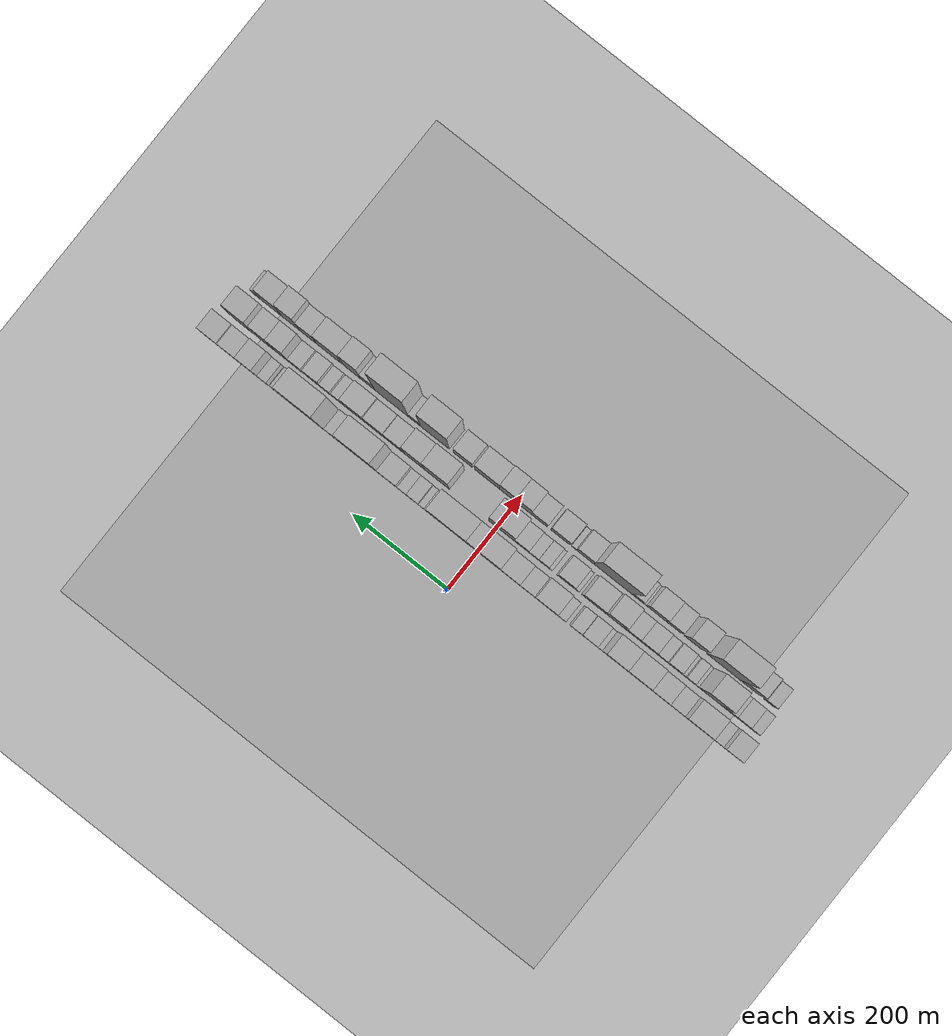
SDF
<?xml version="1.0" encoding="utf-8"?>

<sdf version="1.6">

   <world name="default">

      <gui fullscreen="0">

         <camera name="user_camera">

            <pose>-15 0 4.57585 0 0 0</pose>

            <view_controller>orbit</view_controller>

         </camera>

      </gui>

      <scene>

         <sky>

           <clouds>

             <speed>12</speed>

           </clouds>

         </sky>

         <ambient>0.4 0.4 0.4 1</ambient>

         <background>0.7 0.7 0.7 1</background>

         <shadows>1</shadows>

      </scene>

      <gravity>0 0 -9.8066</gravity>

      <magnetic_field>6e-06 2.3e-05 -4.2e-05</magnetic_field>

      <physics default="0" name="default_physics" type="ode">

         <ode>

            <solver>

               <type>quick</type>

               <iters>10</iters>

               <sor>1.0</sor>

               <use_dynamic_moi_rescaling>0</use_dynamic_moi_rescaling>

            </solver>

            <constraints>

               <cfm>0</cfm>

               <erp>0.2</erp>

               <contact_max_correcting_vel>100</contact_max_correcting_vel>

               <contact_surface_layer>0.001</contact_surface_layer>

            </constraints>

         </ode>

         <max_step_size>0.004</max_step_size>

         <real_time_factor>1</real_time_factor>

         <real_time_update_rate>250</real_time_update_rate>

      </physics>

      <light name="sun" type="directional">

         <cast_shadows>1</cast_shadows>

         <pose>0 0 10 0 0 0</pose>

         <diffuse>0.8 0.8 0.8 1</diffuse>

         <specular>0.2 0.2 0.2 1</specular>

         <attenuation>

            <range>1000</range>

            <constant>0.9</constant>

            <linear>0.01</linear>

            <quadratic>0.001</quadratic>

         </attenuation>

         <direction>-0.5 0.1 -0.9</direction>

      </light>

      <include>

         <name>ground_plane_1</name>

         <uri>model://HANNAS_ground_plane</uri>

         <pose>0 0 0  0 0 0</pose>

      </include>

      <include>

         <name>ground_plane_2</name>

         <uri>model://HANNAS_ground_plane</uri>

         <pose>100 0 0  0 0 0</pose>

      </include>

      <model name="building_1">

         <static>1</static>

         <pose frame="">100.0000 -530.3338 0 0.000000 0.000000 0.000000</pose>

         <link name="link">

            <pose frame="">0 0 33.00 0 0 0</pose>

            <collision name="collision">

               <geometry>

                  <box>

                     <size>40.0000 35.3325 66.0000</size>

                  </box>

               </geometry>

               <max_contacts>10</max_contacts>

               <surface>

                  <contact>

                     <ode/>

                  </contact>

                  <bounce/>

                  <friction>

                     <torsional>

                        <ode/>

                     </torsional>

                     <ode/>

                  </friction>

               </surface>

            </collision>

            <visual name="visual">

               <cast_shadows>0</cast_shadows>

               <geometry>

                  <box>

                     <size>40.0000 35.3325 66.0000</size>

                  </box>

               </geometry>

               <material>

                  <script>

                     <uri>model://HANNAS_wall/materials/scripts</uri>

                     <uri>model://HANNAS_wall/materials/textures</uri>

                     <name>vrc/HANNAS_wall</name>

                  </script>

               </material>

            </visual>

            <self_collide>0</self_collide>

            <enable_wind>0</enable_wind>

            <kinematic>0</kinematic>

         </link>

      </model>

      <model name="building_2">

         <static>1</static>

         <pose frame="">100.0000 -502.6981 0 0.000000 0.000000 0.000000</pose>

         <link name="link">

            <pose frame="">0 0 18.00 0 0 0</pose>

            <collision name="collision">

               <geometry>

                  <box>

                     <size>40.0000 19.9389 36.0000</size>

                  </box>

               </geometry>

               <max_contacts>10</max_contacts>

               <surface>

                  <contact>

                     <ode/>

                  </contact>

                  <bounce/>

                  <friction>

                     <torsional>

                        <ode/>

                     </torsional>

                     <ode/>

                  </friction>

               </surface>

            </collision>

            <visual name="visual">

               <cast_shadows>0</cast_shadows>

               <geometry>

                  <box>

                     <size>40.0000 19.9389 36.0000</size>

                  </box>

               </geometry>

               <material>

                  <script>

                     <uri>model://HANNAS_wall/materials/scripts</uri>

                     <uri>model://HANNAS_wall/materials/textures</uri>

                     <name>vrc/HANNAS_wall</name>

                  </script>

               </material>

            </visual>

            <self_collide>0</self_collide>

            <enable_wind>0</enable_wind>

            <kinematic>0</kinematic>

         </link>

      </model>

      <model name="building_3">

         <static>1</static>

         <pose frame="">100.0000 -488.2948 0 0.000000 0.000000 0.000000</pose>

         <link name="link">

            <pose frame="">0 0 9.00 0 0 0</pose>

            <collision name="collision">

               <geometry>

                  <box>

                     <size>40.0000 8.8676 18.0000</size>

                  </box>

               </geometry>

               <max_contacts>10</max_contacts>

               <surface>

                  <contact>

                     <ode/>

                  </contact>

                  <bounce/>

                  <friction>

                     <torsional>

                        <ode/>

                     </torsional>

                     <ode/>

                  </friction>

               </surface>

            </collision>

            <visual name="visual">

               <cast_shadows>0</cast_shadows>

               <geometry>

                  <box>

                     <size>40.0000 8.8676 18.0000</size>

                  </box>

               </geometry>

               <material>

                  <script>

                     <uri>model://HANNAS_wall/materials/scripts</uri>

                     <uri>model://HANNAS_wall/materials/textures</uri>

                     <name>vrc/HANNAS_wall</name>

                  </script>

               </material>

            </visual>

            <self_collide>0</self_collide>

            <enable_wind>0</enable_wind>

            <kinematic>0</kinematic>

         </link>

      </model>

      <model name="building_4">

         <static>1</static>

         <pose frame="">100.0000 -457.0138 0 0.000000 0.000000 0.000000</pose>

         <link name="link">

            <pose frame="">0 0 45.00 0 0 0</pose>

            <collision name="collision">

               <geometry>

                  <box>

                     <size>40.0000 53.6944 90.0000</size>

                  </box>

               </geometry>

               <max_contacts>10</max_contacts>

               <surface>

                  <contact>

                     <ode/>

                  </contact>

                  <bounce/>

                  <friction>

                     <torsional>

                        <ode/>

                     </torsional>

                     <ode/>

                  </friction>

               </surface>

            </collision>

            <visual name="visual">

               <cast_shadows>0</cast_shadows>

               <geometry>

                  <box>

                     <size>40.0000 53.6944 90.0000</size>

                  </box>

               </geometry>

               <material>

                  <script>

                     <uri>model://HANNAS_wall/materials/scripts</uri>

                     <uri>model://HANNAS_wall/materials/textures</uri>

                     <name>vrc/HANNAS_wall</name>

                  </script>

               </material>

            </visual>

            <self_collide>0</self_collide>

            <enable_wind>0</enable_wind>

            <kinematic>0</kinematic>

         </link>

      </model>

      <model name="building_5">

         <static>1</static>

         <pose frame="">100.0000 -415.0397 0 0.000000 0.000000 0.000000</pose>

         <link name="link">

            <pose frame="">0 0 25.50 0 0 0</pose>

            <collision name="collision">

               <geometry>

                  <box>

                     <size>40.0000 30.2539 51.0000</size>

                  </box>

               </geometry>

               <max_contacts>10</max_contacts>

               <surface>

                  <contact>

                     <ode/>

                  </contact>

                  <bounce/>

                  <friction>

                     <torsional>

                        <ode/>

                     </torsional>

                     <ode/>

                  </friction>

               </surface>

            </collision>

            <visual name="visual">

               <cast_shadows>0</cast_shadows>

               <geometry>

                  <box>

                     <size>40.0000 30.2539 51.0000</size>

                  </box>

               </geometry>

               <material>

                  <script>

                     <uri>model://HANNAS_wall/materials/scripts</uri>

                     <uri>model://HANNAS_wall/materials/textures</uri>

                     <name>vrc/HANNAS_wall</name>

                  </script>

               </material>

            </visual>

            <self_collide>0</self_collide>

            <enable_wind>0</enable_wind>

            <kinematic>0</kinematic>

         </link>

      </model>

      <model name="building_6">

         <static>1</static>

         <pose frame="">100.0000 -377.3122 0 0.000000 0.000000 0.000000</pose>

         <link name="link">

            <pose frame="">0 0 36.00 0 0 0</pose>

            <collision name="collision">

               <geometry>

                  <box>

                     <size>40.0000 39.2010 72.0000</size>

                  </box>

               </geometry>

               <max_contacts>10</max_contacts>

               <surface>

                  <contact>

                     <ode/>

                  </contact>

                  <bounce/>

                  <friction>

                     <torsional>

                        <ode/>

                     </torsional>

                     <ode/>

                  </friction>

               </surface>

            </collision>

            <visual name="visual">

               <cast_shadows>0</cast_shadows>

               <geometry>

                  <box>

                     <size>40.0000 39.2010 72.0000</size>

                  </box>

               </geometry>

               <material>

                  <script>

                     <uri>model://HANNAS_wall/materials/scripts</uri>

                     <uri>model://HANNAS_wall/materials/textures</uri>

                     <name>vrc/HANNAS_wall</name>

                  </script>

               </material>

            </visual>

            <self_collide>0</self_collide>

            <enable_wind>0</enable_wind>

            <kinematic>0</kinematic>

         </link>

      </model>

      <model name="building_7">

         <static>1</static>

         <pose frame="">100.0000 -328.5585 0 0.000000 0.000000 0.000000</pose>

         <link name="link">

            <pose frame="">0 0 61.50 0 0 0</pose>

            <collision name="collision">

               <geometry>

                  <box>

                     <size>40.0000 48.3065 123.0000</size>

                  </box>

               </geometry>

               <max_contacts>10</max_contacts>

               <surface>

                  <contact>

                     <ode/>

                  </contact>

                  <bounce/>

                  <friction>

                     <torsional>

                        <ode/>

                     </torsional>

                     <ode/>

                  </friction>

               </surface>

            </collision>

            <visual name="visual">

               <cast_shadows>0</cast_shadows>

               <geometry>

                  <box>

                     <size>40.0000 48.3065 123.0000</size>

                  </box>

               </geometry>

               <material>

                  <script>

                     <uri>model://HANNAS_wall/materials/scripts</uri>

                     <uri>model://HANNAS_wall/materials/textures</uri>

                     <name>vrc/HANNAS_wall</name>

                  </script>

               </material>

            </visual>

            <self_collide>0</self_collide>

            <enable_wind>0</enable_wind>

            <kinematic>0</kinematic>

         </link>

      </model>

      <model name="building_8">

         <static>1</static>

         <pose frame="">100.0000 -282.7142 0 0.000000 0.000000 0.000000</pose>

         <link name="link">

            <pose frame="">0 0 63.00 0 0 0</pose>

            <collision name="collision">

               <geometry>

                  <box>

                     <size>40.0000 43.3821 126.0000</size>

                  </box>

               </geometry>

               <max_contacts>10</max_contacts>

               <surface>

                  <contact>

                     <ode/>

                  </contact>

                  <bounce/>

                  <friction>

                     <torsional>

                        <ode/>

                     </torsional>

                     <ode/>

                  </friction>

               </surface>

            </collision>

            <visual name="visual">

               <cast_shadows>0</cast_shadows>

               <geometry>

                  <box>

                     <size>40.0000 43.3821 126.0000</size>

                  </box>

               </geometry>

               <material>

                  <script>

                     <uri>model://HANNAS_wall/materials/scripts</uri>

                     <uri>model://HANNAS_wall/materials/textures</uri>

                     <name>vrc/HANNAS_wall</name>

                  </script>

               </material>

            </visual>

            <self_collide>0</self_collide>

            <enable_wind>0</enable_wind>

            <kinematic>0</kinematic>

         </link>

      </model>

      <model name="building_9">

         <static>1</static>

         <pose frame="">100.0000 -255.2567 0 0.000000 0.000000 0.000000</pose>

         <link name="link">

            <pose frame="">0 0 13.50 0 0 0</pose>

            <collision name="collision">

               <geometry>

                  <box>

                     <size>40.0000 11.5329 27.0000</size>

                  </box>

               </geometry>

               <max_contacts>10</max_contacts>

               <surface>

                  <contact>

                     <ode/>

                  </contact>

                  <bounce/>

                  <friction>

                     <torsional>

                        <ode/>

                     </torsional>

                     <ode/>

                  </friction>

               </surface>

            </collision>

            <visual name="visual">

               <cast_shadows>0</cast_shadows>

               <geometry>

                  <box>

                     <size>40.0000 11.5329 27.0000</size>

                  </box>

               </geometry>

               <material>

                  <script>

                     <uri>model://HANNAS_wall/materials/scripts</uri>

                     <uri>model://HANNAS_wall/materials/textures</uri>

                     <name>vrc/HANNAS_wall</name>

                  </script>

               </material>

            </visual>

            <self_collide>0</self_collide>

            <enable_wind>0</enable_wind>

            <kinematic>0</kinematic>

         </link>

      </model>

      <model name="building_10">

         <static>1</static>

         <pose frame="">100.0000 -233.8581 0 0.000000 0.000000 0.000000</pose>

         <link name="link">

            <pose frame="">0 0 28.50 0 0 0</pose>

            <collision name="collision">

               <geometry>

                  <box>

                     <size>40.0000 31.2644 57.0000</size>

                  </box>

               </geometry>

               <max_contacts>10</max_contacts>

               <surface>

                  <contact>

                     <ode/>

                  </contact>

                  <bounce/>

                  <friction>

                     <torsional>

                        <ode/>

                     </torsional>

                     <ode/>

                  </friction>

               </surface>

            </collision>

            <visual name="visual">

               <cast_shadows>0</cast_shadows>

               <geometry>

                  <box>

                     <size>40.0000 31.2644 57.0000</size>

                  </box>

               </geometry>

               <material>

                  <script>

                     <uri>model://HANNAS_wall/materials/scripts</uri>

                     <uri>model://HANNAS_wall/materials/textures</uri>

                     <name>vrc/HANNAS_wall</name>

                  </script>

               </material>

            </visual>

            <self_collide>0</self_collide>

            <enable_wind>0</enable_wind>

            <kinematic>0</kinematic>

         </link>

      </model>

      <model name="building_11">

         <static>1</static>

         <pose frame="">100.0000 -206.1032 0 0.000000 0.000000 0.000000</pose>

         <link name="link">

            <pose frame="">0 0 24.00 0 0 0</pose>

            <collision name="collision">

               <geometry>

                  <box>

                     <size>40.0000 24.2454 48.0000</size>

                  </box>

               </geometry>

               <max_contacts>10</max_contacts>

               <surface>

                  <contact>

                     <ode/>

                  </contact>

                  <bounce/>

                  <friction>

                     <torsional>

                        <ode/>

                     </torsional>

                     <ode/>

                  </friction>

               </surface>

            </collision>

            <visual name="visual">

               <cast_shadows>0</cast_shadows>

               <geometry>

                  <box>

                     <size>40.0000 24.2454 48.0000</size>

                  </box>

               </geometry>

               <material>

                  <script>

                     <uri>model://HANNAS_wall/materials/scripts</uri>

                     <uri>model://HANNAS_wall/materials/textures</uri>

                     <name>vrc/HANNAS_wall</name>

                  </script>

               </material>

            </visual>

            <self_collide>0</self_collide>

            <enable_wind>0</enable_wind>

            <kinematic>0</kinematic>

         </link>

      </model>

      <model name="building_12">

         <static>1</static>

         <pose frame="">100.0000 -174.3278 0 0.000000 0.000000 0.000000</pose>

         <link name="link">

            <pose frame="">0 0 18.00 0 0 0</pose>

            <collision name="collision">

               <geometry>

                  <box>

                     <size>40.0000 21.3055 36.0000</size>

                  </box>

               </geometry>

               <max_contacts>10</max_contacts>

               <surface>

                  <contact>

                     <ode/>

                  </contact>

                  <bounce/>

                  <friction>

                     <torsional>

                        <ode/>

                     </torsional>

                     <ode/>

                  </friction>

               </surface>

            </collision>

            <visual name="visual">

               <cast_shadows>0</cast_shadows>

               <geometry>

                  <box>

                     <size>40.0000 21.3055 36.0000</size>

                  </box>

               </geometry>

               <material>

                  <script>

                     <uri>model://HANNAS_wall/materials/scripts</uri>

                     <uri>model://HANNAS_wall/materials/textures</uri>

                     <name>vrc/HANNAS_wall</name>

                  </script>

               </material>

            </visual>

            <self_collide>0</self_collide>

            <enable_wind>0</enable_wind>

            <kinematic>0</kinematic>

         </link>

      </model>

      <model name="building_13">

         <static>1</static>

         <pose frame="">100.0000 -141.2333 0 0.000000 0.000000 0.000000</pose>

         <link name="link">

            <pose frame="">0 0 60.00 0 0 0</pose>

            <collision name="collision">

               <geometry>

                  <box>

                     <size>40.0000 44.8834 120.0000</size>

                  </box>

               </geometry>

               <max_contacts>10</max_contacts>

               <surface>

                  <contact>

                     <ode/>

                  </contact>

                  <bounce/>

                  <friction>

                     <torsional>

                        <ode/>

                     </torsional>

                     <ode/>

                  </friction>

               </surface>

            </collision>

            <visual name="visual">

               <cast_shadows>0</cast_shadows>

               <geometry>

                  <box>

                     <size>40.0000 44.8834 120.0000</size>

                  </box>

               </geometry>

               <material>

                  <script>

                     <uri>model://HANNAS_wall/materials/scripts</uri>

                     <uri>model://HANNAS_wall/materials/textures</uri>

                     <name>vrc/HANNAS_wall</name>

                  </script>

               </material>

            </visual>

            <self_collide>0</self_collide>

            <enable_wind>0</enable_wind>

            <kinematic>0</kinematic>

         </link>

      </model>

      <model name="building_14">

         <static>1</static>

         <pose frame="">100.0000 -103.5274 0 0.000000 0.000000 0.000000</pose>

         <link name="link">

            <pose frame="">0 0 30.00 0 0 0</pose>

            <collision name="collision">

               <geometry>

                  <box>

                     <size>40.0000 30.5285 60.0000</size>

                  </box>

               </geometry>

               <max_contacts>10</max_contacts>

               <surface>

                  <contact>

                     <ode/>

                  </contact>

                  <bounce/>

                  <friction>

                     <torsional>

                        <ode/>

                     </torsional>

                     <ode/>

                  </friction>

               </surface>

            </collision>

            <visual name="visual">

               <cast_shadows>0</cast_shadows>

               <geometry>

                  <box>

                     <size>40.0000 30.5285 60.0000</size>

                  </box>

               </geometry>

               <material>

                  <script>

                     <uri>model://HANNAS_wall/materials/scripts</uri>

                     <uri>model://HANNAS_wall/materials/textures</uri>

                     <name>vrc/HANNAS_wall</name>

                  </script>

               </material>

            </visual>

            <self_collide>0</self_collide>

            <enable_wind>0</enable_wind>

            <kinematic>0</kinematic>

         </link>

      </model>

      <model name="building_15">

         <static>1</static>

         <pose frame="">100.0000 -67.6410 0 0.000000 0.000000 0.000000</pose>

         <link name="link">

            <pose frame="">0 0 39.00 0 0 0</pose>

            <collision name="collision">

               <geometry>

                  <box>

                     <size>40.0000 41.2443 78.0000</size>

                  </box>

               </geometry>

               <max_contacts>10</max_contacts>

               <surface>

                  <contact>

                     <ode/>

                  </contact>

                  <bounce/>

                  <friction>

                     <torsional>

                        <ode/>

                     </torsional>

                     <ode/>

                  </friction>

               </surface>

            </collision>

            <visual name="visual">

               <cast_shadows>0</cast_shadows>

               <geometry>

                  <box>

                     <size>40.0000 41.2443 78.0000</size>

                  </box>

               </geometry>

               <material>

                  <script>

                     <uri>model://HANNAS_wall/materials/scripts</uri>

                     <uri>model://HANNAS_wall/materials/textures</uri>

                     <name>vrc/HANNAS_wall</name>

                  </script>

               </material>

            </visual>

            <self_collide>0</self_collide>

            <enable_wind>0</enable_wind>

            <kinematic>0</kinematic>

         </link>

      </model>

      <model name="building_16">

         <static>1</static>

         <pose frame="">100.0000 -12.9384 0 0.000000 0.000000 0.000000</pose>

         <link name="link">

            <pose frame="">0 0 99.00 0 0 0</pose>

            <collision name="collision">

               <geometry>

                  <box>

                     <size>40.0000 68.1609 198.0000</size>

                  </box>

               </geometry>

               <max_contacts>10</max_contacts>

               <surface>

                  <contact>

                     <ode/>

                  </contact>

                  <bounce/>

                  <friction>

                     <torsional>

                        <ode/>

                     </torsional>

                     <ode/>

                  </friction>

               </surface>

            </collision>

            <visual name="visual">

               <cast_shadows>0</cast_shadows>

               <geometry>

                  <box>

                     <size>40.0000 68.1609 198.0000</size>

                  </box>

               </geometry>

               <material>

                  <script>

                     <uri>model://HANNAS_wall/materials/scripts</uri>

                     <uri>model://HANNAS_wall/materials/textures</uri>

                     <name>vrc/HANNAS_wall</name>

                  </script>

               </material>

            </visual>

            <self_collide>0</self_collide>

            <enable_wind>0</enable_wind>

            <kinematic>0</kinematic>

         </link>

      </model>

      <model name="building_17">

         <static>1</static>

         <pose frame="">100.0000 60.6066 0 0.000000 0.000000 0.000000</pose>

         <link name="link">

            <pose frame="">0 0 99.00 0 0 0</pose>

            <collision name="collision">

               <geometry>

                  <box>

                     <size>40.0000 78.9291 198.0000</size>

                  </box>

               </geometry>

               <max_contacts>10</max_contacts>

               <surface>

                  <contact>

                     <ode/>

                  </contact>

                  <bounce/>

                  <friction>

                     <torsional>

                        <ode/>

                     </torsional>

                     <ode/>

                  </friction>

               </surface>

            </collision>

            <visual name="visual">

               <cast_shadows>0</cast_shadows>

               <geometry>

                  <box>

                     <size>40.0000 78.9291 198.0000</size>

                  </box>

               </geometry>

               <material>

                  <script>

                     <uri>model://HANNAS_wall/materials/scripts</uri>

                     <uri>model://HANNAS_wall/materials/textures</uri>

                     <name>vrc/HANNAS_wall</name>

                  </script>

               </material>

            </visual>

            <self_collide>0</self_collide>

            <enable_wind>0</enable_wind>

            <kinematic>0</kinematic>

         </link>

      </model>

      <model name="building_18">

         <static>1</static>

         <pose frame="">100.0000 106.1872 0 0.000000 0.000000 0.000000</pose>

         <link name="link">

            <pose frame="">0 0 13.50 0 0 0</pose>

            <collision name="collision">

               <geometry>

                  <box>

                     <size>40.0000 12.2322 27.0000</size>

                  </box>

               </geometry>

               <max_contacts>10</max_contacts>

               <surface>

                  <contact>

                     <ode/>

                  </contact>

                  <bounce/>

                  <friction>

                     <torsional>

                        <ode/>

                     </torsional>

                     <ode/>

                  </friction>

               </surface>

            </collision>

            <visual name="visual">

               <cast_shadows>0</cast_shadows>

               <geometry>

                  <box>

                     <size>40.0000 12.2322 27.0000</size>

                  </box>

               </geometry>

               <material>

                  <script>

                     <uri>model://HANNAS_wall/materials/scripts</uri>

                     <uri>model://HANNAS_wall/materials/textures</uri>

                     <name>vrc/HANNAS_wall</name>

                  </script>

               </material>

            </visual>

            <self_collide>0</self_collide>

            <enable_wind>0</enable_wind>

            <kinematic>0</kinematic>

         </link>

      </model>

      <model name="building_19">

         <static>1</static>

         <pose frame="">100.0000 118.0213 0 0.000000 0.000000 0.000000</pose>

         <link name="link">

            <pose frame="">0 0 13.50 0 0 0</pose>

            <collision name="collision">

               <geometry>

                  <box>

                     <size>40.0000 11.4359 27.0000</size>

                  </box>

               </geometry>

               <max_contacts>10</max_contacts>

               <surface>

                  <contact>

                     <ode/>

                  </contact>

                  <bounce/>

                  <friction>

                     <torsional>

                        <ode/>

                     </torsional>

                     <ode/>

                  </friction>

               </surface>

            </collision>

            <visual name="visual">

               <cast_shadows>0</cast_shadows>

               <geometry>

                  <box>

                     <size>40.0000 11.4359 27.0000</size>

                  </box>

               </geometry>

               <material>

                  <script>

                     <uri>model://HANNAS_wall/materials/scripts</uri>

                     <uri>model://HANNAS_wall/materials/textures</uri>

                     <name>vrc/HANNAS_wall</name>

                  </script>

               </material>

            </visual>

            <self_collide>0</self_collide>

            <enable_wind>0</enable_wind>

            <kinematic>0</kinematic>

         </link>

      </model>

      <model name="building_20">

         <static>1</static>

         <pose frame="">100.0000 136.0296 0 0.000000 0.000000 0.000000</pose>

         <link name="link">

            <pose frame="">0 0 24.00 0 0 0</pose>

            <collision name="collision">

               <geometry>

                  <box>

                     <size>40.0000 24.5808 48.0000</size>

                  </box>

               </geometry>

               <max_contacts>10</max_contacts>

               <surface>

                  <contact>

                     <ode/>

                  </contact>

                  <bounce/>

                  <friction>

                     <torsional>

                        <ode/>

                     </torsional>

                     <ode/>

                  </friction>

               </surface>

            </collision>

            <visual name="visual">

               <cast_shadows>0</cast_shadows>

               <geometry>

                  <box>

                     <size>40.0000 24.5808 48.0000</size>

                  </box>

               </geometry>

               <material>

                  <script>

                     <uri>model://HANNAS_wall/materials/scripts</uri>

                     <uri>model://HANNAS_wall/materials/textures</uri>

                     <name>vrc/HANNAS_wall</name>

                  </script>

               </material>

            </visual>

            <self_collide>0</self_collide>

            <enable_wind>0</enable_wind>

            <kinematic>0</kinematic>

         </link>

      </model>

      <model name="building_21">

         <static>1</static>

         <pose frame="">100.0000 158.2399 0 0.000000 0.000000 0.000000</pose>

         <link name="link">

            <pose frame="">0 0 18.00 0 0 0</pose>

            <collision name="collision">

               <geometry>

                  <box>

                     <size>40.0000 19.8397 36.0000</size>

                  </box>

               </geometry>

               <max_contacts>10</max_contacts>

               <surface>

                  <contact>

                     <ode/>

                  </contact>

                  <bounce/>

                  <friction>

                     <torsional>

                        <ode/>

                     </torsional>

                     <ode/>

                  </friction>

               </surface>

            </collision>

            <visual name="visual">

               <cast_shadows>0</cast_shadows>

               <geometry>

                  <box>

                     <size>40.0000 19.8397 36.0000</size>

                  </box>

               </geometry>

               <material>

                  <script>

                     <uri>model://HANNAS_wall/materials/scripts</uri>

                     <uri>model://HANNAS_wall/materials/textures</uri>

                     <name>vrc/HANNAS_wall</name>

                  </script>

               </material>

            </visual>

            <self_collide>0</self_collide>

            <enable_wind>0</enable_wind>

            <kinematic>0</kinematic>

         </link>

      </model>

      <model name="building_22">

         <static>1</static>

         <pose frame="">100.0000 188.0186 0 0.000000 0.000000 0.000000</pose>

         <link name="link">

            <pose frame="">0 0 36.00 0 0 0</pose>

            <collision name="collision">

               <geometry>

                  <box>

                     <size>40.0000 39.7177 72.0000</size>

                  </box>

               </geometry>

               <max_contacts>10</max_contacts>

               <surface>

                  <contact>

                     <ode/>

                  </contact>

                  <bounce/>

                  <friction>

                     <torsional>

                        <ode/>

                     </torsional>

                     <ode/>

                  </friction>

               </surface>

            </collision>

            <visual name="visual">

               <cast_shadows>0</cast_shadows>

               <geometry>

                  <box>

                     <size>40.0000 39.7177 72.0000</size>

                  </box>

               </geometry>

               <material>

                  <script>

                     <uri>model://HANNAS_wall/materials/scripts</uri>

                     <uri>model://HANNAS_wall/materials/textures</uri>

                     <name>vrc/HANNAS_wall</name>

                  </script>

               </material>

            </visual>

            <self_collide>0</self_collide>

            <enable_wind>0</enable_wind>

            <kinematic>0</kinematic>

         </link>

      </model>

      <model name="building_23">

         <static>1</static>

         <pose frame="">100.0000 242.9697 0 0.000000 0.000000 0.000000</pose>

         <link name="link">

            <pose frame="">0 0 111.00 0 0 0</pose>

            <collision name="collision">

               <geometry>

                  <box>

                     <size>40.0000 70.1845 222.0000</size>

                  </box>

               </geometry>

               <max_contacts>10</max_contacts>

               <surface>

                  <contact>

                     <ode/>

                  </contact>

                  <bounce/>

                  <friction>

                     <torsional>

                        <ode/>

                     </torsional>

                     <ode/>

                  </friction>

               </surface>

            </collision>

            <visual name="visual">

               <cast_shadows>0</cast_shadows>

               <geometry>

                  <box>

                     <size>40.0000 70.1845 222.0000</size>

                  </box>

               </geometry>

               <material>

                  <script>

                     <uri>model://HANNAS_wall/materials/scripts</uri>

                     <uri>model://HANNAS_wall/materials/textures</uri>

                     <name>vrc/HANNAS_wall</name>

                  </script>

               </material>

            </visual>

            <self_collide>0</self_collide>

            <enable_wind>0</enable_wind>

            <kinematic>0</kinematic>

         </link>

      </model>

      <model name="building_24">

         <static>1</static>

         <pose frame="">100.0000 294.7581 0 0.000000 0.000000 0.000000</pose>

         <link name="link">

            <pose frame="">0 0 52.50 0 0 0</pose>

            <collision name="collision">

               <geometry>

                  <box>

                     <size>40.0000 33.3922 105.0000</size>

                  </box>

               </geometry>

               <max_contacts>10</max_contacts>

               <surface>

                  <contact>

                     <ode/>

                  </contact>

                  <bounce/>

                  <friction>

                     <torsional>

                        <ode/>

                     </torsional>

                     <ode/>

                  </friction>

               </surface>

            </collision>

            <visual name="visual">

               <cast_shadows>0</cast_shadows>

               <geometry>

                  <box>

                     <size>40.0000 33.3922 105.0000</size>

                  </box>

               </geometry>

               <material>

                  <script>

                     <uri>model://HANNAS_wall/materials/scripts</uri>

                     <uri>model://HANNAS_wall/materials/textures</uri>

                     <name>vrc/HANNAS_wall</name>

                  </script>

               </material>

            </visual>

            <self_collide>0</self_collide>

            <enable_wind>0</enable_wind>

            <kinematic>0</kinematic>

         </link>

      </model>

      <model name="building_25">

         <static>1</static>

         <pose frame="">100.0000 358.0408 0 0.000000 0.000000 0.000000</pose>

         <link name="link">

            <pose frame="">0 0 109.50 0 0 0</pose>

            <collision name="collision">

               <geometry>

                  <box>

                     <size>40.0000 73.1731 219.0000</size>

                  </box>

               </geometry>

               <max_contacts>10</max_contacts>

               <surface>

                  <contact>

                     <ode/>

                  </contact>

                  <bounce/>

                  <friction>

                     <torsional>

                        <ode/>

                     </torsional>

                     <ode/>

                  </friction>

               </surface>

            </collision>

            <visual name="visual">

               <cast_shadows>0</cast_shadows>

               <geometry>

                  <box>

                     <size>40.0000 73.1731 219.0000</size>

                  </box>

               </geometry>

               <material>

                  <script>

                     <uri>model://HANNAS_wall/materials/scripts</uri>

                     <uri>model://HANNAS_wall/materials/textures</uri>

                     <name>vrc/HANNAS_wall</name>

                  </script>

               </material>

            </visual>

            <self_collide>0</self_collide>

            <enable_wind>0</enable_wind>

            <kinematic>0</kinematic>

         </link>

      </model>

      <model name="building_26">

         <static>1</static>

         <pose frame="">100.0000 418.4843 0 0.000000 0.000000 0.000000</pose>

         <link name="link">

            <pose frame="">0 0 24.00 0 0 0</pose>

            <collision name="collision">

               <geometry>

                  <box>

                     <size>40.0000 27.7140 48.0000</size>

                  </box>

               </geometry>

               <max_contacts>10</max_contacts>

               <surface>

                  <contact>

                     <ode/>

                  </contact>

                  <bounce/>

                  <friction>

                     <torsional>

                        <ode/>

                     </torsional>

                     <ode/>

                  </friction>

               </surface>

            </collision>

            <visual name="visual">

               <cast_shadows>0</cast_shadows>

               <geometry>

                  <box>

                     <size>40.0000 27.7140 48.0000</size>

                  </box>

               </geometry>

               <material>

                  <script>

                     <uri>model://HANNAS_wall/materials/scripts</uri>

                     <uri>model://HANNAS_wall/materials/textures</uri>

                     <name>vrc/HANNAS_wall</name>

                  </script>

               </material>

            </visual>

            <self_collide>0</self_collide>

            <enable_wind>0</enable_wind>

            <kinematic>0</kinematic>

         </link>

      </model>

      <model name="building_27">

         <static>1</static>

         <pose frame="">100.0000 452.0103 0 0.000000 0.000000 0.000000</pose>

         <link name="link">

            <pose frame="">0 0 16.50 0 0 0</pose>

            <collision name="collision">

               <geometry>

                  <box>

                     <size>40.0000 19.3379 33.0000</size>

                  </box>

               </geometry>

               <max_contacts>10</max_contacts>

               <surface>

                  <contact>

                     <ode/>

                  </contact>

                  <bounce/>

                  <friction>

                     <torsional>

                        <ode/>

                     </torsional>

                     <ode/>

                  </friction>

               </surface>

            </collision>

            <visual name="visual">

               <cast_shadows>0</cast_shadows>

               <geometry>

                  <box>

                     <size>40.0000 19.3379 33.0000</size>

                  </box>

               </geometry>

               <material>

                  <script>

                     <uri>model://HANNAS_wall/materials/scripts</uri>

                     <uri>model://HANNAS_wall/materials/textures</uri>

                     <name>vrc/HANNAS_wall</name>

                  </script>

               </material>

            </visual>

            <self_collide>0</self_collide>

            <enable_wind>0</enable_wind>

            <kinematic>0</kinematic>

         </link>

      </model>

      <model name="building_28">

         <static>1</static>

         <pose frame="">100.0000 478.5497 0 0.000000 0.000000 0.000000</pose>

         <link name="link">

            <pose frame="">0 0 48.00 0 0 0</pose>

            <collision name="collision">

               <geometry>

                  <box>

                     <size>40.0000 33.7410 96.0000</size>

                  </box>

               </geometry>

               <max_contacts>10</max_contacts>

               <surface>

                  <contact>

                     <ode/>

                  </contact>

                  <bounce/>

                  <friction>

                     <torsional>

                        <ode/>

                     </torsional>

                     <ode/>

                  </friction>

               </surface>

            </collision>

            <visual name="visual">

               <cast_shadows>0</cast_shadows>

               <geometry>

                  <box>

                     <size>40.0000 33.7410 96.0000</size>

                  </box>

               </geometry>

               <material>

                  <script>

                     <uri>model://HANNAS_wall/materials/scripts</uri>

                     <uri>model://HANNAS_wall/materials/textures</uri>

                     <name>vrc/HANNAS_wall</name>

                  </script>

               </material>

            </visual>

            <self_collide>0</self_collide>

            <enable_wind>0</enable_wind>

            <kinematic>0</kinematic>

         </link>

      </model>

      <model name="building_29">

         <static>1</static>

         <pose frame="">100.0000 520.0226 0 0.000000 0.000000 0.000000</pose>

         <link name="link">

            <pose frame="">0 0 31.50 0 0 0</pose>

            <collision name="collision">

               <geometry>

                  <box>

                     <size>40.0000 37.2048 63.0000</size>

                  </box>

               </geometry>

               <max_contacts>10</max_contacts>

               <surface>

                  <contact>

                     <ode/>

                  </contact>

                  <bounce/>

                  <friction>

                     <torsional>

                        <ode/>

                     </torsional>

                     <ode/>

                  </friction>

               </surface>

            </collision>

            <visual name="visual">

               <cast_shadows>0</cast_shadows>

               <geometry>

                  <box>

                     <size>40.0000 37.2048 63.0000</size>

                  </box>

               </geometry>

               <material>

                  <script>

                     <uri>model://HANNAS_wall/materials/scripts</uri>

                     <uri>model://HANNAS_wall/materials/textures</uri>

                     <name>vrc/HANNAS_wall</name>

                  </script>

               </material>

            </visual>

            <self_collide>0</self_collide>

            <enable_wind>0</enable_wind>

            <kinematic>0</kinematic>

         </link>

      </model>

      <model name="building_30">

         <static>1</static>

         <pose frame="">100.0000 558.9845 0 0.000000 0.000000 0.000000</pose>

         <link name="link">

            <pose frame="">0 0 34.50 0 0 0</pose>

            <collision name="collision">

               <geometry>

                  <box>

                     <size>40.0000 40.7190 69.0000</size>

                  </box>

               </geometry>

               <max_contacts>10</max_contacts>

               <surface>

                  <contact>

                     <ode/>

                  </contact>

                  <bounce/>

                  <friction>

                     <torsional>

                        <ode/>

                     </torsional>

                     <ode/>

                  </friction>

               </surface>

            </collision>

            <visual name="visual">

               <cast_shadows>0</cast_shadows>

               <geometry>

                  <box>

                     <size>40.0000 40.7190 69.0000</size>

                  </box>

               </geometry>

               <material>

                  <script>

                     <uri>model://HANNAS_wall/materials/scripts</uri>

                     <uri>model://HANNAS_wall/materials/textures</uri>

                     <name>vrc/HANNAS_wall</name>

                  </script>

               </material>

            </visual>

            <self_collide>0</self_collide>

            <enable_wind>0</enable_wind>

            <kinematic>0</kinematic>

         </link>

      </model>

      <model name="building_31">

         <static>1</static>

         <pose frame="">152.0000 -537.5515 0 0.000000 0.000000 0.000000</pose>

         <link name="link">

            <pose frame="">0 0 18.00 0 0 0</pose>

            <collision name="collision">

               <geometry>

                  <box>

                     <size>40.0000 20.8969 36.0000</size>

                  </box>

               </geometry>

               <max_contacts>10</max_contacts>

               <surface>

                  <contact>

                     <ode/>

                  </contact>

                  <bounce/>

                  <friction>

                     <torsional>

                        <ode/>

                     </torsional>

                     <ode/>

                  </friction>

               </surface>

            </collision>

            <visual name="visual">

               <cast_shadows>0</cast_shadows>

               <geometry>

                  <box>

                     <size>40.0000 20.8969 36.0000</size>

                  </box>

               </geometry>

               <material>

                  <script>

                     <uri>model://HANNAS_wall/materials/scripts</uri>

                     <uri>model://HANNAS_wall/materials/textures</uri>

                     <name>vrc/HANNAS_wall</name>

                  </script>

               </material>

            </visual>

            <self_collide>0</self_collide>

            <enable_wind>0</enable_wind>

            <kinematic>0</kinematic>

         </link>

      </model>

      <model name="building_32">

         <static>1</static>

         <pose frame="">152.0000 -512.8496 0 0.000000 0.000000 0.000000</pose>

         <link name="link">

            <pose frame="">0 0 24.00 0 0 0</pose>

            <collision name="collision">

               <geometry>

                  <box>

                     <size>40.0000 28.5069 48.0000</size>

                  </box>

               </geometry>

               <max_contacts>10</max_contacts>

               <surface>

                  <contact>

                     <ode/>

                  </contact>

                  <bounce/>

                  <friction>

                     <torsional>

                        <ode/>

                     </torsional>

                     <ode/>

                  </friction>

               </surface>

            </collision>

            <visual name="visual">

               <cast_shadows>0</cast_shadows>

               <geometry>

                  <box>

                     <size>40.0000 28.5069 48.0000</size>

                  </box>

               </geometry>

               <material>

                  <script>

                     <uri>model://HANNAS_wall/materials/scripts</uri>

                     <uri>model://HANNAS_wall/materials/textures</uri>

                     <name>vrc/HANNAS_wall</name>

                  </script>

               </material>

            </visual>

            <self_collide>0</self_collide>

            <enable_wind>0</enable_wind>

            <kinematic>0</kinematic>

         </link>

      </model>

      <model name="building_33">

         <static>1</static>

         <pose frame="">152.0000 -485.3992 0 0.000000 0.000000 0.000000</pose>

         <link name="link">

            <pose frame="">0 0 24.00 0 0 0</pose>

            <collision name="collision">

               <geometry>

                  <box>

                     <size>40.0000 26.3939 48.0000</size>

                  </box>

               </geometry>

               <max_contacts>10</max_contacts>

               <surface>

                  <contact>

                     <ode/>

                  </contact>

                  <bounce/>

                  <friction>

                     <torsional>

                        <ode/>

                     </torsional>

                     <ode/>

                  </friction>

               </surface>

            </collision>

            <visual name="visual">

               <cast_shadows>0</cast_shadows>

               <geometry>

                  <box>

                     <size>40.0000 26.3939 48.0000</size>

                  </box>

               </geometry>

               <material>

                  <script>

                     <uri>model://HANNAS_wall/materials/scripts</uri>

                     <uri>model://HANNAS_wall/materials/textures</uri>

                     <name>vrc/HANNAS_wall</name>

                  </script>

               </material>

            </visual>

            <self_collide>0</self_collide>

            <enable_wind>0</enable_wind>

            <kinematic>0</kinematic>

         </link>

      </model>

      <model name="building_34">

         <static>1</static>

         <pose frame="">152.0000 -447.6264 0 0.000000 0.000000 0.000000</pose>

         <link name="link">

            <pose frame="">0 0 75.00 0 0 0</pose>

            <collision name="collision">

               <geometry>

                  <box>

                     <size>40.0000 49.1517 150.0000</size>

                  </box>

               </geometry>

               <max_contacts>10</max_contacts>

               <surface>

                  <contact>

                     <ode/>

                  </contact>

                  <bounce/>

                  <friction>

                     <torsional>

                        <ode/>

                     </torsional>

                     <ode/>

                  </friction>

               </surface>

            </collision>

            <visual name="visual">

               <cast_shadows>0</cast_shadows>

               <geometry>

                  <box>

                     <size>40.0000 49.1517 150.0000</size>

                  </box>

               </geometry>

               <material>

                  <script>

                     <uri>model://HANNAS_wall/materials/scripts</uri>

                     <uri>model://HANNAS_wall/materials/textures</uri>

                     <name>vrc/HANNAS_wall</name>

                  </script>

               </material>

            </visual>

            <self_collide>0</self_collide>

            <enable_wind>0</enable_wind>

            <kinematic>0</kinematic>

         </link>

      </model>

      <model name="building_35">

         <static>1</static>

         <pose frame="">152.0000 -418.7044 0 0.000000 0.000000 0.000000</pose>

         <link name="link">

            <pose frame="">0 0 9.00 0 0 0</pose>

            <collision name="collision">

               <geometry>

                  <box>

                     <size>40.0000 8.6922 18.0000</size>

                  </box>

               </geometry>

               <max_contacts>10</max_contacts>

               <surface>

                  <contact>

                     <ode/>

                  </contact>

                  <bounce/>

                  <friction>

                     <torsional>

                        <ode/>

                     </torsional>

                     <ode/>

                  </friction>

               </surface>

            </collision>

            <visual name="visual">

               <cast_shadows>0</cast_shadows>

               <geometry>

                  <box>

                     <size>40.0000 8.6922 18.0000</size>

                  </box>

               </geometry>

               <material>

                  <script>

                     <uri>model://HANNAS_wall/materials/scripts</uri>

                     <uri>model://HANNAS_wall/materials/textures</uri>

                     <name>vrc/HANNAS_wall</name>

                  </script>

               </material>

            </visual>

            <self_collide>0</self_collide>

            <enable_wind>0</enable_wind>

            <kinematic>0</kinematic>

         </link>

      </model>

      <model name="building_36">

         <static>1</static>

         <pose frame="">152.0000 -404.8493 0 0.000000 0.000000 0.000000</pose>

         <link name="link">

            <pose frame="">0 0 18.00 0 0 0</pose>

            <collision name="collision">

               <geometry>

                  <box>

                     <size>40.0000 19.0181 36.0000</size>

                  </box>

               </geometry>

               <max_contacts>10</max_contacts>

               <surface>

                  <contact>

                     <ode/>

                  </contact>

                  <bounce/>

                  <friction>

                     <torsional>

                        <ode/>

                     </torsional>

                     <ode/>

                  </friction>

               </surface>

            </collision>

            <visual name="visual">

               <cast_shadows>0</cast_shadows>

               <geometry>

                  <box>

                     <size>40.0000 19.0181 36.0000</size>

                  </box>

               </geometry>

               <material>

                  <script>

                     <uri>model://HANNAS_wall/materials/scripts</uri>

                     <uri>model://HANNAS_wall/materials/textures</uri>

                     <name>vrc/HANNAS_wall</name>

                  </script>

               </material>

            </visual>

            <self_collide>0</self_collide>

            <enable_wind>0</enable_wind>

            <kinematic>0</kinematic>

         </link>

      </model>

      <model name="building_37">

         <static>1</static>

         <pose frame="">152.0000 -390.2916 0 0.000000 0.000000 0.000000</pose>

         <link name="link">

            <pose frame="">0 0 12.00 0 0 0</pose>

            <collision name="collision">

               <geometry>

                  <box>

                     <size>40.0000 10.0972 24.0000</size>

                  </box>

               </geometry>

               <max_contacts>10</max_contacts>

               <surface>

                  <contact>

                     <ode/>

                  </contact>

                  <bounce/>

                  <friction>

                     <torsional>

                        <ode/>

                     </torsional>

                     <ode/>

                  </friction>

               </surface>

            </collision>

            <visual name="visual">

               <cast_shadows>0</cast_shadows>

               <geometry>

                  <box>

                     <size>40.0000 10.0972 24.0000</size>

                  </box>

               </geometry>

               <material>

                  <script>

                     <uri>model://HANNAS_wall/materials/scripts</uri>

                     <uri>model://HANNAS_wall/materials/textures</uri>

                     <name>vrc/HANNAS_wall</name>

                  </script>

               </material>

            </visual>

            <self_collide>0</self_collide>

            <enable_wind>0</enable_wind>

            <kinematic>0</kinematic>

         </link>

      </model>

      <model name="building_38">

         <static>1</static>

         <pose frame="">152.0000 -370.4043 0 0.000000 0.000000 0.000000</pose>

         <link name="link">

            <pose frame="">0 0 25.50 0 0 0</pose>

            <collision name="collision">

               <geometry>

                  <box>

                     <size>40.0000 29.6774 51.0000</size>

                  </box>

               </geometry>

               <max_contacts>10</max_contacts>

               <surface>

                  <contact>

                     <ode/>

                  </contact>

                  <bounce/>

                  <friction>

                     <torsional>

                        <ode/>

                     </torsional>

                     <ode/>

                  </friction>

               </surface>

            </collision>

            <visual name="visual">

               <cast_shadows>0</cast_shadows>

               <geometry>

                  <box>

                     <size>40.0000 29.6774 51.0000</size>

                  </box>

               </geometry>

               <material>

                  <script>

                     <uri>model://HANNAS_wall/materials/scripts</uri>

                     <uri>model://HANNAS_wall/materials/textures</uri>

                     <name>vrc/HANNAS_wall</name>

                  </script>

               </material>

            </visual>

            <self_collide>0</self_collide>

            <enable_wind>0</enable_wind>

            <kinematic>0</kinematic>

         </link>

      </model>

      <model name="building_39">

         <static>1</static>

         <pose frame="">152.0000 -344.0261 0 0.000000 0.000000 0.000000</pose>

         <link name="link">

            <pose frame="">0 0 19.50 0 0 0</pose>

            <collision name="collision">

               <geometry>

                  <box>

                     <size>40.0000 23.0791 39.0000</size>

                  </box>

               </geometry>

               <max_contacts>10</max_contacts>

               <surface>

                  <contact>

                     <ode/>

                  </contact>

                  <bounce/>

                  <friction>

                     <torsional>

                        <ode/>

                     </torsional>

                     <ode/>

                  </friction>

               </surface>

            </collision>

            <visual name="visual">

               <cast_shadows>0</cast_shadows>

               <geometry>

                  <box>

                     <size>40.0000 23.0791 39.0000</size>

                  </box>

               </geometry>

               <material>

                  <script>

                     <uri>model://HANNAS_wall/materials/scripts</uri>

                     <uri>model://HANNAS_wall/materials/textures</uri>

                     <name>vrc/HANNAS_wall</name>

                  </script>

               </material>

            </visual>

            <self_collide>0</self_collide>

            <enable_wind>0</enable_wind>

            <kinematic>0</kinematic>

         </link>

      </model>

      <model name="building_40">

         <static>1</static>

         <pose frame="">152.0000 -315.2339 0 0.000000 0.000000 0.000000</pose>

         <link name="link">

            <pose frame="">0 0 30.00 0 0 0</pose>

            <collision name="collision">

               <geometry>

                  <box>

                     <size>40.0000 34.5054 60.0000</size>

                  </box>

               </geometry>

               <max_contacts>10</max_contacts>

               <surface>

                  <contact>

                     <ode/>

                  </contact>

                  <bounce/>

                  <friction>

                     <torsional>

                        <ode/>

                     </torsional>

                     <ode/>

                  </friction>

               </surface>

            </collision>

            <visual name="visual">

               <cast_shadows>0</cast_shadows>

               <geometry>

                  <box>

                     <size>40.0000 34.5054 60.0000</size>

                  </box>

               </geometry>

               <material>

                  <script>

                     <uri>model://HANNAS_wall/materials/scripts</uri>

                     <uri>model://HANNAS_wall/materials/textures</uri>

                     <name>vrc/HANNAS_wall</name>

                  </script>

               </material>

            </visual>

            <self_collide>0</self_collide>

            <enable_wind>0</enable_wind>

            <kinematic>0</kinematic>

         </link>

      </model>

      <model name="building_41">

         <static>1</static>

         <pose frame="">152.0000 -280.9853 0 0.000000 0.000000 0.000000</pose>

         <link name="link">

            <pose frame="">0 0 30.00 0 0 0</pose>

            <collision name="collision">

               <geometry>

                  <box>

                     <size>40.0000 33.9917 60.0000</size>

                  </box>

               </geometry>

               <max_contacts>10</max_contacts>

               <surface>

                  <contact>

                     <ode/>

                  </contact>

                  <bounce/>

                  <friction>

                     <torsional>

                        <ode/>

                     </torsional>

                     <ode/>

                  </friction>

               </surface>

            </collision>

            <visual name="visual">

               <cast_shadows>0</cast_shadows>

               <geometry>

                  <box>

                     <size>40.0000 33.9917 60.0000</size>

                  </box>

               </geometry>

               <material>

                  <script>

                     <uri>model://HANNAS_wall/materials/scripts</uri>

                     <uri>model://HANNAS_wall/materials/textures</uri>

                     <name>vrc/HANNAS_wall</name>

                  </script>

               </material>

            </visual>

            <self_collide>0</self_collide>

            <enable_wind>0</enable_wind>

            <kinematic>0</kinematic>

         </link>

      </model>

      <model name="building_42">

         <static>1</static>

         <pose frame="">152.0000 -244.4302 0 0.000000 0.000000 0.000000</pose>

         <link name="link">

            <pose frame="">0 0 61.50 0 0 0</pose>

            <collision name="collision">

               <geometry>

                  <box>

                     <size>40.0000 39.1185 123.0000</size>

                  </box>

               </geometry>

               <max_contacts>10</max_contacts>

               <surface>

                  <contact>

                     <ode/>

                  </contact>

                  <bounce/>

                  <friction>

                     <torsional>

                        <ode/>

                     </torsional>

                     <ode/>

                  </friction>

               </surface>

            </collision>

            <visual name="visual">

               <cast_shadows>0</cast_shadows>

               <geometry>

                  <box>

                     <size>40.0000 39.1185 123.0000</size>

                  </box>

               </geometry>

               <material>

                  <script>

                     <uri>model://HANNAS_wall/materials/scripts</uri>

                     <uri>model://HANNAS_wall/materials/textures</uri>

                     <name>vrc/HANNAS_wall</name>

                  </script>

               </material>

            </visual>

            <self_collide>0</self_collide>

            <enable_wind>0</enable_wind>

            <kinematic>0</kinematic>

         </link>

      </model>

      <model name="building_43">

         <static>1</static>

         <pose frame="">152.0000 -201.6564 0 0.000000 0.000000 0.000000</pose>

         <link name="link">

            <pose frame="">0 0 40.50 0 0 0</pose>

            <collision name="collision">

               <geometry>

                  <box>

                     <size>40.0000 46.4292 81.0000</size>

                  </box>

               </geometry>

               <max_contacts>10</max_contacts>

               <surface>

                  <contact>

                     <ode/>

                  </contact>

                  <bounce/>

                  <friction>

                     <torsional>

                        <ode/>

                     </torsional>

                     <ode/>

                  </friction>

               </surface>

            </collision>

            <visual name="visual">

               <cast_shadows>0</cast_shadows>

               <geometry>

                  <box>

                     <size>40.0000 46.4292 81.0000</size>

                  </box>

               </geometry>

               <material>

                  <script>

                     <uri>model://HANNAS_wall/materials/scripts</uri>

                     <uri>model://HANNAS_wall/materials/textures</uri>

                     <name>vrc/HANNAS_wall</name>

                  </script>

               </material>

            </visual>

            <self_collide>0</self_collide>

            <enable_wind>0</enable_wind>

            <kinematic>0</kinematic>

         </link>

      </model>

      <model name="building_44">

         <static>1</static>

         <pose frame="">152.0000 -167.5456 0 0.000000 0.000000 0.000000</pose>

         <link name="link">

            <pose frame="">0 0 12.00 0 0 0</pose>

            <collision name="collision">

               <geometry>

                  <box>

                     <size>40.0000 9.7924 24.0000</size>

                  </box>

               </geometry>

               <max_contacts>10</max_contacts>

               <surface>

                  <contact>

                     <ode/>

                  </contact>

                  <bounce/>

                  <friction>

                     <torsional>

                        <ode/>

                     </torsional>

                     <ode/>

                  </friction>

               </surface>

            </collision>

            <visual name="visual">

               <cast_shadows>0</cast_shadows>

               <geometry>

                  <box>

                     <size>40.0000 9.7924 24.0000</size>

                  </box>

               </geometry>

               <material>

                  <script>

                     <uri>model://HANNAS_wall/materials/scripts</uri>

                     <uri>model://HANNAS_wall/materials/textures</uri>

                     <name>vrc/HANNAS_wall</name>

                  </script>

               </material>

            </visual>

            <self_collide>0</self_collide>

            <enable_wind>0</enable_wind>

            <kinematic>0</kinematic>

         </link>

      </model>

      <model name="building_45">

         <static>1</static>

         <pose frame="">152.0000 -144.4393 0 0.000000 0.000000 0.000000</pose>

         <link name="link">

            <pose frame="">0 0 33.00 0 0 0</pose>

            <collision name="collision">

               <geometry>

                  <box>

                     <size>40.0000 36.4202 66.0000</size>

                  </box>

               </geometry>

               <max_contacts>10</max_contacts>

               <surface>

                  <contact>

                     <ode/>

                  </contact>

                  <bounce/>

                  <friction>

                     <torsional>

                        <ode/>

                     </torsional>

                     <ode/>

                  </friction>

               </surface>

            </collision>

            <visual name="visual">

               <cast_shadows>0</cast_shadows>

               <geometry>

                  <box>

                     <size>40.0000 36.4202 66.0000</size>

                  </box>

               </geometry>

               <material>

                  <script>

                     <uri>model://HANNAS_wall/materials/scripts</uri>

                     <uri>model://HANNAS_wall/materials/textures</uri>

                     <name>vrc/HANNAS_wall</name>

                  </script>

               </material>

            </visual>

            <self_collide>0</self_collide>

            <enable_wind>0</enable_wind>

            <kinematic>0</kinematic>

         </link>

      </model>

      <model name="building_46">

         <static>1</static>

         <pose frame="">152.0000 -112.5041 0 0.000000 0.000000 0.000000</pose>

         <link name="link">

            <pose frame="">0 0 9.00 0 0 0</pose>

            <collision name="collision">

               <geometry>

                  <box>

                     <size>40.0000 7.4502 18.0000</size>

                  </box>

               </geometry>

               <max_contacts>10</max_contacts>

               <surface>

                  <contact>

                     <ode/>

                  </contact>

                  <bounce/>

                  <friction>

                     <torsional>

                        <ode/>

                     </torsional>

                     <ode/>

                  </friction>

               </surface>

            </collision>

            <visual name="visual">

               <cast_shadows>0</cast_shadows>

               <geometry>

                  <box>

                     <size>40.0000 7.4502 18.0000</size>

                  </box>

               </geometry>

               <material>

                  <script>

                     <uri>model://HANNAS_wall/materials/scripts</uri>

                     <uri>model://HANNAS_wall/materials/textures</uri>

                     <name>vrc/HANNAS_wall</name>

                  </script>

               </material>

            </visual>

            <self_collide>0</self_collide>

            <enable_wind>0</enable_wind>

            <kinematic>0</kinematic>

         </link>

      </model>

      <model name="building_47">

         <static>1</static>

         <pose frame="">152.0000 -97.9111 0 0.000000 0.000000 0.000000</pose>

         <link name="link">

            <pose frame="">0 0 21.00 0 0 0</pose>

            <collision name="collision">

               <geometry>

                  <box>

                     <size>40.0000 21.7357 42.0000</size>

                  </box>

               </geometry>

               <max_contacts>10</max_contacts>

               <surface>

                  <contact>

                     <ode/>

                  </contact>

                  <bounce/>

                  <friction>

                     <torsional>

                        <ode/>

                     </torsional>

                     <ode/>

                  </friction>

               </surface>

            </collision>

            <visual name="visual">

               <cast_shadows>0</cast_shadows>

               <geometry>

                  <box>

                     <size>40.0000 21.7357 42.0000</size>

                  </box>

               </geometry>

               <material>

                  <script>

                     <uri>model://HANNAS_wall/materials/scripts</uri>

                     <uri>model://HANNAS_wall/materials/textures</uri>

                     <name>vrc/HANNAS_wall</name>

                  </script>

               </material>

            </visual>

            <self_collide>0</self_collide>

            <enable_wind>0</enable_wind>

            <kinematic>0</kinematic>

         </link>

      </model>

      <model name="building_48">

         <static>1</static>

         <pose frame="">152.0000 -76.6915 0 0.000000 0.000000 0.000000</pose>

         <link name="link">

            <pose frame="">0 0 18.00 0 0 0</pose>

            <collision name="collision">

               <geometry>

                  <box>

                     <size>40.0000 20.7035 36.0000</size>

                  </box>

               </geometry>

               <max_contacts>10</max_contacts>

               <surface>

                  <contact>

                     <ode/>

                  </contact>

                  <bounce/>

                  <friction>

                     <torsional>

                        <ode/>

                     </torsional>

                     <ode/>

                  </friction>

               </surface>

            </collision>

            <visual name="visual">

               <cast_shadows>0</cast_shadows>

               <geometry>

                  <box>

                     <size>40.0000 20.7035 36.0000</size>

                  </box>

               </geometry>

               <material>

                  <script>

                     <uri>model://HANNAS_wall/materials/scripts</uri>

                     <uri>model://HANNAS_wall/materials/textures</uri>

                     <name>vrc/HANNAS_wall</name>

                  </script>

               </material>

            </visual>

            <self_collide>0</self_collide>

            <enable_wind>0</enable_wind>

            <kinematic>0</kinematic>

         </link>

      </model>

      <model name="building_49">

         <static>1</static>

         <pose frame="">152.0000 -51.4175 0 0.000000 0.000000 0.000000</pose>

         <link name="link">

            <pose frame="">0 0 27.00 0 0 0</pose>

            <collision name="collision">

               <geometry>

                  <box>

                     <size>40.0000 29.8444 54.0000</size>

                  </box>

               </geometry>

               <max_contacts>10</max_contacts>

               <surface>

                  <contact>

                     <ode/>

                  </contact>

                  <bounce/>

                  <friction>

                     <torsional>

                        <ode/>

                     </torsional>

                     <ode/>

                  </friction>

               </surface>

            </collision>

            <visual name="visual">

               <cast_shadows>0</cast_shadows>

               <geometry>

                  <box>

                     <size>40.0000 29.8444 54.0000</size>

                  </box>

               </geometry>

               <material>

                  <script>

                     <uri>model://HANNAS_wall/materials/scripts</uri>

                     <uri>model://HANNAS_wall/materials/textures</uri>

                     <name>vrc/HANNAS_wall</name>

                  </script>

               </material>

            </visual>

            <self_collide>0</self_collide>

            <enable_wind>0</enable_wind>

            <kinematic>0</kinematic>

         </link>

      </model>

      <model name="building_50">

         <static>1</static>

         <pose frame="">152.0000 -9.5820 0 0.000000 0.000000 0.000000</pose>

         <link name="link">

            <pose frame="">0 0 70.50 0 0 0</pose>

            <collision name="collision">

               <geometry>

                  <box>

                     <size>40.0000 53.8266 141.0000</size>

                  </box>

               </geometry>

               <max_contacts>10</max_contacts>

               <surface>

                  <contact>

                     <ode/>

                  </contact>

                  <bounce/>

                  <friction>

                     <torsional>

                        <ode/>

                     </torsional>

                     <ode/>

                  </friction>

               </surface>

            </collision>

            <visual name="visual">

               <cast_shadows>0</cast_shadows>

               <geometry>

                  <box>

                     <size>40.0000 53.8266 141.0000</size>

                  </box>

               </geometry>

               <material>

                  <script>

                     <uri>model://HANNAS_wall/materials/scripts</uri>

                     <uri>model://HANNAS_wall/materials/textures</uri>

                     <name>vrc/HANNAS_wall</name>

                  </script>

               </material>

            </visual>

            <self_collide>0</self_collide>

            <enable_wind>0</enable_wind>

            <kinematic>0</kinematic>

         </link>

      </model>

      <model name="building_51">

         <static>1</static>

         <pose frame="">152.0000 126.9348 0 0.000000 0.000000 0.000000</pose>

         <link name="link">

            <pose frame="">0 0 72.00 0 0 0</pose>

            <collision name="collision">

               <geometry>

                  <box>

                     <size>40.0000 53.0690 144.0000</size>

                  </box>

               </geometry>

               <max_contacts>10</max_contacts>

               <surface>

                  <contact>

                     <ode/>

                  </contact>

                  <bounce/>

                  <friction>

                     <torsional>

                        <ode/>

                     </torsional>

                     <ode/>

                  </friction>

               </surface>

            </collision>

            <visual name="visual">

               <cast_shadows>0</cast_shadows>

               <geometry>

                  <box>

                     <size>40.0000 53.0690 144.0000</size>

                  </box>

               </geometry>

               <material>

                  <script>

                     <uri>model://HANNAS_wall/materials/scripts</uri>

                     <uri>model://HANNAS_wall/materials/textures</uri>

                     <name>vrc/HANNAS_wall</name>

                  </script>

               </material>

            </visual>

            <self_collide>0</self_collide>

            <enable_wind>0</enable_wind>

            <kinematic>0</kinematic>

         </link>

      </model>

      <model name="building_52">

         <static>1</static>

         <pose frame="">152.0000 174.4519 0 0.000000 0.000000 0.000000</pose>

         <link name="link">

            <pose frame="">0 0 63.00 0 0 0</pose>

            <collision name="collision">

               <geometry>

                  <box>

                     <size>40.0000 41.9653 126.0000</size>

                  </box>

               </geometry>

               <max_contacts>10</max_contacts>

               <surface>

                  <contact>

                     <ode/>

                  </contact>

                  <bounce/>

                  <friction>

                     <torsional>

                        <ode/>

                     </torsional>

                     <ode/>

                  </friction>

               </surface>

            </collision>

            <visual name="visual">

               <cast_shadows>0</cast_shadows>

               <geometry>

                  <box>

                     <size>40.0000 41.9653 126.0000</size>

                  </box>

               </geometry>

               <material>

                  <script>

                     <uri>model://HANNAS_wall/materials/scripts</uri>

                     <uri>model://HANNAS_wall/materials/textures</uri>

                     <name>vrc/HANNAS_wall</name>

                  </script>

               </material>

            </visual>

            <self_collide>0</self_collide>

            <enable_wind>0</enable_wind>

            <kinematic>0</kinematic>

         </link>

      </model>

      <model name="building_53">

         <static>1</static>

         <pose frame="">152.0000 215.9594 0 0.000000 0.000000 0.000000</pose>

         <link name="link">

            <pose frame="">0 0 34.50 0 0 0</pose>

            <collision name="collision">

               <geometry>

                  <box>

                     <size>40.0000 41.0497 69.0000</size>

                  </box>

               </geometry>

               <max_contacts>10</max_contacts>

               <surface>

                  <contact>

                     <ode/>

                  </contact>

                  <bounce/>

                  <friction>

                     <torsional>

                        <ode/>

                     </torsional>

                     <ode/>

                  </friction>

               </surface>

            </collision>

            <visual name="visual">

               <cast_shadows>0</cast_shadows>

               <geometry>

                  <box>

                     <size>40.0000 41.0497 69.0000</size>

                  </box>

               </geometry>

               <material>

                  <script>

                     <uri>model://HANNAS_wall/materials/scripts</uri>

                     <uri>model://HANNAS_wall/materials/textures</uri>

                     <name>vrc/HANNAS_wall</name>

                  </script>

               </material>

            </visual>

            <self_collide>0</self_collide>

            <enable_wind>0</enable_wind>

            <kinematic>0</kinematic>

         </link>

      </model>

      <model name="building_54">

         <static>1</static>

         <pose frame="">152.0000 257.1814 0 0.000000 0.000000 0.000000</pose>

         <link name="link">

            <pose frame="">0 0 37.50 0 0 0</pose>

            <collision name="collision">

               <geometry>

                  <box>

                     <size>40.0000 41.3941 75.0000</size>

                  </box>

               </geometry>

               <max_contacts>10</max_contacts>

               <surface>

                  <contact>

                     <ode/>

                  </contact>

                  <bounce/>

                  <friction>

                     <torsional>

                        <ode/>

                     </torsional>

                     <ode/>

                  </friction>

               </surface>

            </collision>

            <visual name="visual">

               <cast_shadows>0</cast_shadows>

               <geometry>

                  <box>

                     <size>40.0000 41.3941 75.0000</size>

                  </box>

               </geometry>

               <material>

                  <script>

                     <uri>model://HANNAS_wall/materials/scripts</uri>

                     <uri>model://HANNAS_wall/materials/textures</uri>

                     <name>vrc/HANNAS_wall</name>

                  </script>

               </material>

            </visual>

            <self_collide>0</self_collide>

            <enable_wind>0</enable_wind>

            <kinematic>0</kinematic>

         </link>

      </model>

      <model name="building_55">

         <static>1</static>

         <pose frame="">152.0000 301.3035 0 0.000000 0.000000 0.000000</pose>

         <link name="link">

            <pose frame="">0 0 43.50 0 0 0</pose>

            <collision name="collision">

               <geometry>

                  <box>

                     <size>40.0000 46.8502 87.0000</size>

                  </box>

               </geometry>

               <max_contacts>10</max_contacts>

               <surface>

                  <contact>

                     <ode/>

                  </contact>

                  <bounce/>

                  <friction>

                     <torsional>

                        <ode/>

                     </torsional>

                     <ode/>

                  </friction>

               </surface>

            </collision>

            <visual name="visual">

               <cast_shadows>0</cast_shadows>

               <geometry>

                  <box>

                     <size>40.0000 46.8502 87.0000</size>

                  </box>

               </geometry>

               <material>

                  <script>

                     <uri>model://HANNAS_wall/materials/scripts</uri>

                     <uri>model://HANNAS_wall/materials/textures</uri>

                     <name>vrc/HANNAS_wall</name>

                  </script>

               </material>

            </visual>

            <self_collide>0</self_collide>

            <enable_wind>0</enable_wind>

            <kinematic>0</kinematic>

         </link>

      </model>

      <model name="building_56">

         <static>1</static>

         <pose frame="">152.0000 336.2653 0 0.000000 0.000000 0.000000</pose>

         <link name="link">

            <pose frame="">0 0 21.00 0 0 0</pose>

            <collision name="collision">

               <geometry>

                  <box>

                     <size>40.0000 23.0735 42.0000</size>

                  </box>

               </geometry>

               <max_contacts>10</max_contacts>

               <surface>

                  <contact>

                     <ode/>

                  </contact>

                  <bounce/>

                  <friction>

                     <torsional>

                        <ode/>

                     </torsional>

                     <ode/>

                  </friction>

               </surface>

            </collision>

            <visual name="visual">

               <cast_shadows>0</cast_shadows>

               <geometry>

                  <box>

                     <size>40.0000 23.0735 42.0000</size>

                  </box>

               </geometry>

               <material>

                  <script>

                     <uri>model://HANNAS_wall/materials/scripts</uri>

                     <uri>model://HANNAS_wall/materials/textures</uri>

                     <name>vrc/HANNAS_wall</name>

                  </script>

               </material>

            </visual>

            <self_collide>0</self_collide>

            <enable_wind>0</enable_wind>

            <kinematic>0</kinematic>

         </link>

      </model>

      <model name="building_57">

         <static>1</static>

         <pose frame="">152.0000 361.8748 0 0.000000 0.000000 0.000000</pose>

         <link name="link">

            <pose frame="">0 0 19.50 0 0 0</pose>

            <collision name="collision">

               <geometry>

                  <box>

                     <size>40.0000 22.1456 39.0000</size>

                  </box>

               </geometry>

               <max_contacts>10</max_contacts>

               <surface>

                  <contact>

                     <ode/>

                  </contact>

                  <bounce/>

                  <friction>

                     <torsional>

                        <ode/>

                     </torsional>

                     <ode/>

                  </friction>

               </surface>

            </collision>

            <visual name="visual">

               <cast_shadows>0</cast_shadows>

               <geometry>

                  <box>

                     <size>40.0000 22.1456 39.0000</size>

                  </box>

               </geometry>

               <material>

                  <script>

                     <uri>model://HANNAS_wall/materials/scripts</uri>

                     <uri>model://HANNAS_wall/materials/textures</uri>

                     <name>vrc/HANNAS_wall</name>

                  </script>

               </material>

            </visual>

            <self_collide>0</self_collide>

            <enable_wind>0</enable_wind>

            <kinematic>0</kinematic>

         </link>

      </model>

      <model name="building_58">

         <static>1</static>

         <pose frame="">152.0000 388.9664 0 0.000000 0.000000 0.000000</pose>

         <link name="link">

            <pose frame="">0 0 30.00 0 0 0</pose>

            <collision name="collision">

               <geometry>

                  <box>

                     <size>40.0000 32.0376 60.0000</size>

                  </box>

               </geometry>

               <max_contacts>10</max_contacts>

               <surface>

                  <contact>

                     <ode/>

                  </contact>

                  <bounce/>

                  <friction>

                     <torsional>

                        <ode/>

                     </torsional>

                     <ode/>

                  </friction>

               </surface>

            </collision>

            <visual name="visual">

               <cast_shadows>0</cast_shadows>

               <geometry>

                  <box>

                     <size>40.0000 32.0376 60.0000</size>

                  </box>

               </geometry>

               <material>

                  <script>

                     <uri>model://HANNAS_wall/materials/scripts</uri>

                     <uri>model://HANNAS_wall/materials/textures</uri>

                     <name>vrc/HANNAS_wall</name>

                  </script>

               </material>

            </visual>

            <self_collide>0</self_collide>

            <enable_wind>0</enable_wind>

            <kinematic>0</kinematic>

         </link>

      </model>

      <model name="building_59">

         <static>1</static>

         <pose frame="">152.0000 422.7655 0 0.000000 0.000000 0.000000</pose>

         <link name="link">

            <pose frame="">0 0 25.50 0 0 0</pose>

            <collision name="collision">

               <geometry>

                  <box>

                     <size>40.0000 27.5606 51.0000</size>

                  </box>

               </geometry>

               <max_contacts>10</max_contacts>

               <surface>

                  <contact>

                     <ode/>

                  </contact>

                  <bounce/>

                  <friction>

                     <torsional>

                        <ode/>

                     </torsional>

                     <ode/>

                  </friction>

               </surface>

            </collision>

            <visual name="visual">

               <cast_shadows>0</cast_shadows>

               <geometry>

                  <box>

                     <size>40.0000 27.5606 51.0000</size>

                  </box>

               </geometry>

               <material>

                  <script>

                     <uri>model://HANNAS_wall/materials/scripts</uri>

                     <uri>model://HANNAS_wall/materials/textures</uri>

                     <name>vrc/HANNAS_wall</name>

                  </script>

               </material>

            </visual>

            <self_collide>0</self_collide>

            <enable_wind>0</enable_wind>

            <kinematic>0</kinematic>

         </link>

      </model>

      <model name="building_60">

         <static>1</static>

         <pose frame="">152.0000 456.7086 0 0.000000 0.000000 0.000000</pose>

         <link name="link">

            <pose frame="">0 0 51.00 0 0 0</pose>

            <collision name="collision">

               <geometry>

                  <box>

                     <size>40.0000 34.3255 102.0000</size>

                  </box>

               </geometry>

               <max_contacts>10</max_contacts>

               <surface>

                  <contact>

                     <ode/>

                  </contact>

                  <bounce/>

                  <friction>

                     <torsional>

                        <ode/>

                     </torsional>

                     <ode/>

                  </friction>

               </surface>

            </collision>

            <visual name="visual">

               <cast_shadows>0</cast_shadows>

               <geometry>

                  <box>

                     <size>40.0000 34.3255 102.0000</size>

                  </box>

               </geometry>

               <material>

                  <script>

                     <uri>model://HANNAS_wall/materials/scripts</uri>

                     <uri>model://HANNAS_wall/materials/textures</uri>

                     <name>vrc/HANNAS_wall</name>

                  </script>

               </material>

            </visual>

            <self_collide>0</self_collide>

            <enable_wind>0</enable_wind>

            <kinematic>0</kinematic>

         </link>

      </model>

      <model name="building_61">

         <static>1</static>

         <pose frame="">152.0000 491.1172 0 0.000000 0.000000 0.000000</pose>

         <link name="link">

            <pose frame="">0 0 51.00 0 0 0</pose>

            <collision name="collision">

               <geometry>

                  <box>

                     <size>40.0000 34.4919 102.0000</size>

                  </box>

               </geometry>

               <max_contacts>10</max_contacts>

               <surface>

                  <contact>

                     <ode/>

                  </contact>

                  <bounce/>

                  <friction>

                     <torsional>

                        <ode/>

                     </torsional>

                     <ode/>

                  </friction>

               </surface>

            </collision>

            <visual name="visual">

               <cast_shadows>0</cast_shadows>

               <geometry>

                  <box>

                     <size>40.0000 34.4919 102.0000</size>

                  </box>

               </geometry>

               <material>

                  <script>

                     <uri>model://HANNAS_wall/materials/scripts</uri>

                     <uri>model://HANNAS_wall/materials/textures</uri>

                     <name>vrc/HANNAS_wall</name>

                  </script>

               </material>

            </visual>

            <self_collide>0</self_collide>

            <enable_wind>0</enable_wind>

            <kinematic>0</kinematic>

         </link>

      </model>

      <model name="building_62">

         <static>1</static>

         <pose frame="">152.0000 536.3195 0 0.000000 0.000000 0.000000</pose>

         <link name="link">

            <pose frame="">0 0 58.50 0 0 0</pose>

            <collision name="collision">

               <geometry>

                  <box>

                     <size>40.0000 45.9126 117.0000</size>

                  </box>

               </geometry>

               <max_contacts>10</max_contacts>

               <surface>

                  <contact>

                     <ode/>

                  </contact>

                  <bounce/>

                  <friction>

                     <torsional>

                        <ode/>

                     </torsional>

                     <ode/>

                  </friction>

               </surface>

            </collision>

            <visual name="visual">

               <cast_shadows>0</cast_shadows>

               <geometry>

                  <box>

                     <size>40.0000 45.9126 117.0000</size>

                  </box>

               </geometry>

               <material>

                  <script>

                     <uri>model://HANNAS_wall/materials/scripts</uri>

                     <uri>model://HANNAS_wall/materials/textures</uri>

                     <name>vrc/HANNAS_wall</name>

                  </script>

               </material>

            </visual>

            <self_collide>0</self_collide>

            <enable_wind>0</enable_wind>

            <kinematic>0</kinematic>

         </link>

      </model>

      <model name="building_63">

         <static>1</static>

         <pose frame="">204.0000 -531.6019 0 0.000000 0.000000 0.000000</pose>

         <link name="link">

            <pose frame="">0 0 19.50 0 0 0</pose>

            <collision name="collision">

               <geometry>

                  <box>

                     <size>40.0000 22.7963 39.0000</size>

                  </box>

               </geometry>

               <max_contacts>10</max_contacts>

               <surface>

                  <contact>

                     <ode/>

                  </contact>

                  <bounce/>

                  <friction>

                     <torsional>

                        <ode/>

                     </torsional>

                     <ode/>

                  </friction>

               </surface>

            </collision>

            <visual name="visual">

               <cast_shadows>0</cast_shadows>

               <geometry>

                  <box>

                     <size>40.0000 22.7963 39.0000</size>

                  </box>

               </geometry>

               <material>

                  <script>

                     <uri>model://HANNAS_wall/materials/scripts</uri>

                     <uri>model://HANNAS_wall/materials/textures</uri>

                     <name>vrc/HANNAS_wall</name>

                  </script>

               </material>

            </visual>

            <self_collide>0</self_collide>

            <enable_wind>0</enable_wind>

            <kinematic>0</kinematic>

         </link>

      </model>

      <model name="building_64">

         <static>1</static>

         <pose frame="">204.0000 -491.3380 0 0.000000 0.000000 0.000000</pose>

         <link name="link">

            <pose frame="">0 0 39.00 0 0 0</pose>

            <collision name="collision">

               <geometry>

                  <box>

                     <size>40.0000 39.7314 78.0000</size>

                  </box>

               </geometry>

               <max_contacts>10</max_contacts>

               <surface>

                  <contact>

                     <ode/>

                  </contact>

                  <bounce/>

                  <friction>

                     <torsional>

                        <ode/>

                     </torsional>

                     <ode/>

                  </friction>

               </surface>

            </collision>

            <visual name="visual">

               <cast_shadows>0</cast_shadows>

               <geometry>

                  <box>

                     <size>40.0000 39.7314 78.0000</size>

                  </box>

               </geometry>

               <material>

                  <script>

                     <uri>model://HANNAS_wall/materials/scripts</uri>

                     <uri>model://HANNAS_wall/materials/textures</uri>

                     <name>vrc/HANNAS_wall</name>

                  </script>

               </material>

            </visual>

            <self_collide>0</self_collide>

            <enable_wind>0</enable_wind>

            <kinematic>0</kinematic>

         </link>

      </model>

      <model name="building_65">

         <static>1</static>

         <pose frame="">204.0000 -435.4657 0 0.000000 0.000000 0.000000</pose>

         <link name="link">

            <pose frame="">0 0 91.50 0 0 0</pose>

            <collision name="collision">

               <geometry>

                  <box>

                     <size>40.0000 72.0133 183.0000</size>

                  </box>

               </geometry>

               <max_contacts>10</max_contacts>

               <surface>

                  <contact>

                     <ode/>

                  </contact>

                  <bounce/>

                  <friction>

                     <torsional>

                        <ode/>

                     </torsional>

                     <ode/>

                  </friction>

               </surface>

            </collision>

            <visual name="visual">

               <cast_shadows>0</cast_shadows>

               <geometry>

                  <box>

                     <size>40.0000 72.0133 183.0000</size>

                  </box>

               </geometry>

               <material>

                  <script>

                     <uri>model://HANNAS_wall/materials/scripts</uri>

                     <uri>model://HANNAS_wall/materials/textures</uri>

                     <name>vrc/HANNAS_wall</name>

                  </script>

               </material>

            </visual>

            <self_collide>0</self_collide>

            <enable_wind>0</enable_wind>

            <kinematic>0</kinematic>

         </link>

      </model>

      <model name="building_66">

         <static>1</static>

         <pose frame="">204.0000 -371.6864 0 0.000000 0.000000 0.000000</pose>

         <link name="link">

            <pose frame="">0 0 51.00 0 0 0</pose>

            <collision name="collision">

               <geometry>

                  <box>

                     <size>40.0000 37.5453 102.0000</size>

                  </box>

               </geometry>

               <max_contacts>10</max_contacts>

               <surface>

                  <contact>

                     <ode/>

                  </contact>

                  <bounce/>

                  <friction>

                     <torsional>

                        <ode/>

                     </torsional>

                     <ode/>

                  </friction>

               </surface>

            </collision>

            <visual name="visual">

               <cast_shadows>0</cast_shadows>

               <geometry>

                  <box>

                     <size>40.0000 37.5453 102.0000</size>

                  </box>

               </geometry>

               <material>

                  <script>

                     <uri>model://HANNAS_wall/materials/scripts</uri>

                     <uri>model://HANNAS_wall/materials/textures</uri>

                     <name>vrc/HANNAS_wall</name>

                  </script>

               </material>

            </visual>

            <self_collide>0</self_collide>

            <enable_wind>0</enable_wind>

            <kinematic>0</kinematic>

         </link>

      </model>

      <model name="building_67">

         <static>1</static>

         <pose frame="">204.0000 -329.6819 0 0.000000 0.000000 0.000000</pose>

         <link name="link">

            <pose frame="">0 0 28.50 0 0 0</pose>

            <collision name="collision">

               <geometry>

                  <box>

                     <size>40.0000 32.4638 57.0000</size>

                  </box>

               </geometry>

               <max_contacts>10</max_contacts>

               <surface>

                  <contact>

                     <ode/>

                  </contact>

                  <bounce/>

                  <friction>

                     <torsional>

                        <ode/>

                     </torsional>

                     <ode/>

                  </friction>

               </surface>

            </collision>

            <visual name="visual">

               <cast_shadows>0</cast_shadows>

               <geometry>

                  <box>

                     <size>40.0000 32.4638 57.0000</size>

                  </box>

               </geometry>

               <material>

                  <script>

                     <uri>model://HANNAS_wall/materials/scripts</uri>

                     <uri>model://HANNAS_wall/materials/textures</uri>

                     <name>vrc/HANNAS_wall</name>

                  </script>

               </material>

            </visual>

            <self_collide>0</self_collide>

            <enable_wind>0</enable_wind>

            <kinematic>0</kinematic>

         </link>

      </model>

      <model name="building_68">

         <static>1</static>

         <pose frame="">204.0000 -293.4402 0 0.000000 0.000000 0.000000</pose>

         <link name="link">

            <pose frame="">0 0 34.50 0 0 0</pose>

            <collision name="collision">

               <geometry>

                  <box>

                     <size>40.0000 40.0195 69.0000</size>

                  </box>

               </geometry>

               <max_contacts>10</max_contacts>

               <surface>

                  <contact>

                     <ode/>

                  </contact>

                  <bounce/>

                  <friction>

                     <torsional>

                        <ode/>

                     </torsional>

                     <ode/>

                  </friction>

               </surface>

            </collision>

            <visual name="visual">

               <cast_shadows>0</cast_shadows>

               <geometry>

                  <box>

                     <size>40.0000 40.0195 69.0000</size>

                  </box>

               </geometry>

               <material>

                  <script>

                     <uri>model://HANNAS_wall/materials/scripts</uri>

                     <uri>model://HANNAS_wall/materials/textures</uri>

                     <name>vrc/HANNAS_wall</name>

                  </script>

               </material>

            </visual>

            <self_collide>0</self_collide>

            <enable_wind>0</enable_wind>

            <kinematic>0</kinematic>

         </link>

      </model>

      <model name="building_69">

         <static>1</static>

         <pose frame="">204.0000 -270.0618 0 0.000000 0.000000 0.000000</pose>

         <link name="link">

            <pose frame="">0 0 7.50 0 0 0</pose>

            <collision name="collision">

               <geometry>

                  <box>

                     <size>40.0000 6.7374 15.0000</size>

                  </box>

               </geometry>

               <max_contacts>10</max_contacts>

               <surface>

                  <contact>

                     <ode/>

                  </contact>

                  <bounce/>

                  <friction>

                     <torsional>

                        <ode/>

                     </torsional>

                     <ode/>

                  </friction>

               </surface>

            </collision>

            <visual name="visual">

               <cast_shadows>0</cast_shadows>

               <geometry>

                  <box>

                     <size>40.0000 6.7374 15.0000</size>

                  </box>

               </geometry>

               <material>

                  <script>

                     <uri>model://HANNAS_wall/materials/scripts</uri>

                     <uri>model://HANNAS_wall/materials/textures</uri>

                     <name>vrc/HANNAS_wall</name>

                  </script>

               </material>

            </visual>

            <self_collide>0</self_collide>

            <enable_wind>0</enable_wind>

            <kinematic>0</kinematic>

         </link>

      </model>

      <model name="building_70">

         <static>1</static>

         <pose frame="">204.0000 -254.5823 0 0.000000 0.000000 0.000000</pose>

         <link name="link">

            <pose frame="">0 0 21.00 0 0 0</pose>

            <collision name="collision">

               <geometry>

                  <box>

                     <size>40.0000 24.2216 42.0000</size>

                  </box>

               </geometry>

               <max_contacts>10</max_contacts>

               <surface>

                  <contact>

                     <ode/>

                  </contact>

                  <bounce/>

                  <friction>

                     <torsional>

                        <ode/>

                     </torsional>

                     <ode/>

                  </friction>

               </surface>

            </collision>

            <visual name="visual">

               <cast_shadows>0</cast_shadows>

               <geometry>

                  <box>

                     <size>40.0000 24.2216 42.0000</size>

                  </box>

               </geometry>

               <material>

                  <script>

                     <uri>model://HANNAS_wall/materials/scripts</uri>

                     <uri>model://HANNAS_wall/materials/textures</uri>

                     <name>vrc/HANNAS_wall</name>

                  </script>

               </material>

            </visual>

            <self_collide>0</self_collide>

            <enable_wind>0</enable_wind>

            <kinematic>0</kinematic>

         </link>

      </model>

      <model name="building_71">

         <static>1</static>

         <pose frame="">204.0000 -201.8177 0 0.000000 0.000000 0.000000</pose>

         <link name="link">

            <pose frame="">0 0 111.00 0 0 0</pose>

            <collision name="collision">

               <geometry>

                  <box>

                     <size>40.0000 81.3077 222.0000</size>

                  </box>

               </geometry>

               <max_contacts>10</max_contacts>

               <surface>

                  <contact>

                     <ode/>

                  </contact>

                  <bounce/>

                  <friction>

                     <torsional>

                        <ode/>

                     </torsional>

                     <ode/>

                  </friction>

               </surface>

            </collision>

            <visual name="visual">

               <cast_shadows>0</cast_shadows>

               <geometry>

                  <box>

                     <size>40.0000 81.3077 222.0000</size>

                  </box>

               </geometry>

               <material>

                  <script>

                     <uri>model://HANNAS_wall/materials/scripts</uri>

                     <uri>model://HANNAS_wall/materials/textures</uri>

                     <name>vrc/HANNAS_wall</name>

                  </script>

               </material>

            </visual>

            <self_collide>0</self_collide>

            <enable_wind>0</enable_wind>

            <kinematic>0</kinematic>

         </link>

      </model>

      <model name="building_72">

         <static>1</static>

         <pose frame="">204.0000 -143.2729 0 0.000000 0.000000 0.000000</pose>

         <link name="link">

            <pose frame="">0 0 34.50 0 0 0</pose>

            <collision name="collision">

               <geometry>

                  <box>

                     <size>40.0000 35.7818 69.0000</size>

                  </box>

               </geometry>

               <max_contacts>10</max_contacts>

               <surface>

                  <contact>

                     <ode/>

                  </contact>

                  <bounce/>

                  <friction>

                     <torsional>

                        <ode/>

                     </torsional>

                     <ode/>

                  </friction>

               </surface>

            </collision>

            <visual name="visual">

               <cast_shadows>0</cast_shadows>

               <geometry>

                  <box>

                     <size>40.0000 35.7818 69.0000</size>

                  </box>

               </geometry>

               <material>

                  <script>

                     <uri>model://HANNAS_wall/materials/scripts</uri>

                     <uri>model://HANNAS_wall/materials/textures</uri>

                     <name>vrc/HANNAS_wall</name>

                  </script>

               </material>

            </visual>

            <self_collide>0</self_collide>

            <enable_wind>0</enable_wind>

            <kinematic>0</kinematic>

         </link>

      </model>

      <model name="building_73">

         <static>1</static>

         <pose frame="">204.0000 -120.2430 0 0.000000 0.000000 0.000000</pose>

         <link name="link">

            <pose frame="">0 0 10.50 0 0 0</pose>

            <collision name="collision">

               <geometry>

                  <box>

                     <size>40.0000 10.2780 21.0000</size>

                  </box>

               </geometry>

               <max_contacts>10</max_contacts>

               <surface>

                  <contact>

                     <ode/>

                  </contact>

                  <bounce/>

                  <friction>

                     <torsional>

                        <ode/>

                     </torsional>

                     <ode/>

                  </friction>

               </surface>

            </collision>

            <visual name="visual">

               <cast_shadows>0</cast_shadows>

               <geometry>

                  <box>

                     <size>40.0000 10.2780 21.0000</size>

                  </box>

               </geometry>

               <material>

                  <script>

                     <uri>model://HANNAS_wall/materials/scripts</uri>

                     <uri>model://HANNAS_wall/materials/textures</uri>

                     <name>vrc/HANNAS_wall</name>

                  </script>

               </material>

            </visual>

            <self_collide>0</self_collide>

            <enable_wind>0</enable_wind>

            <kinematic>0</kinematic>

         </link>

      </model>

      <model name="building_74">

         <static>1</static>

         <pose frame="">204.0000 -91.7794 0 0.000000 0.000000 0.000000</pose>

         <link name="link">

            <pose frame="">0 0 34.50 0 0 0</pose>

            <collision name="collision">

               <geometry>

                  <box>

                     <size>40.0000 40.6491 69.0000</size>

                  </box>

               </geometry>

               <max_contacts>10</max_contacts>

               <surface>

                  <contact>

                     <ode/>

                  </contact>

                  <bounce/>

                  <friction>

                     <torsional>

                        <ode/>

                     </torsional>

                     <ode/>

                  </friction>

               </surface>

            </collision>

            <visual name="visual">

               <cast_shadows>0</cast_shadows>

               <geometry>

                  <box>

                     <size>40.0000 40.6491 69.0000</size>

                  </box>

               </geometry>

               <material>

                  <script>

                     <uri>model://HANNAS_wall/materials/scripts</uri>

                     <uri>model://HANNAS_wall/materials/textures</uri>

                     <name>vrc/HANNAS_wall</name>

                  </script>

               </material>

            </visual>

            <self_collide>0</self_collide>

            <enable_wind>0</enable_wind>

            <kinematic>0</kinematic>

         </link>

      </model>

      <model name="building_75">

         <static>1</static>

         <pose frame="">204.0000 -47.5161 0 0.000000 0.000000 0.000000</pose>

         <link name="link">

            <pose frame="">0 0 33.00 0 0 0</pose>

            <collision name="collision">

               <geometry>

                  <box>

                     <size>40.0000 33.8776 66.0000</size>

                  </box>

               </geometry>

               <max_contacts>10</max_contacts>

               <surface>

                  <contact>

                     <ode/>

                  </contact>

                  <bounce/>

                  <friction>

                     <torsional>

                        <ode/>

                     </torsional>

                     <ode/>

                  </friction>

               </surface>

            </collision>

            <visual name="visual">

               <cast_shadows>0</cast_shadows>

               <geometry>

                  <box>

                     <size>40.0000 33.8776 66.0000</size>

                  </box>

               </geometry>

               <material>

                  <script>

                     <uri>model://HANNAS_wall/materials/scripts</uri>

                     <uri>model://HANNAS_wall/materials/textures</uri>

                     <name>vrc/HANNAS_wall</name>

                  </script>

               </material>

            </visual>

            <self_collide>0</self_collide>

            <enable_wind>0</enable_wind>

            <kinematic>0</kinematic>

         </link>

      </model>

      <model name="building_76">

         <static>1</static>

         <pose frame="">204.0000 -13.7447 0 0.000000 0.000000 0.000000</pose>

         <link name="link">

            <pose frame="">0 0 52.50 0 0 0</pose>

            <collision name="collision">

               <geometry>

                  <box>

                     <size>40.0000 33.6651 105.0000</size>

                  </box>

               </geometry>

               <max_contacts>10</max_contacts>

               <surface>

                  <contact>

                     <ode/>

                  </contact>

                  <bounce/>

                  <friction>

                     <torsional>

                        <ode/>

                     </torsional>

                     <ode/>

                  </friction>

               </surface>

            </collision>

            <visual name="visual">

               <cast_shadows>0</cast_shadows>

               <geometry>

                  <box>

                     <size>40.0000 33.6651 105.0000</size>

                  </box>

               </geometry>

               <material>

                  <script>

                     <uri>model://HANNAS_wall/materials/scripts</uri>

                     <uri>model://HANNAS_wall/materials/textures</uri>

                     <name>vrc/HANNAS_wall</name>

                  </script>

               </material>

            </visual>

            <self_collide>0</self_collide>

            <enable_wind>0</enable_wind>

            <kinematic>0</kinematic>

         </link>

      </model>

      <model name="building_77">

         <static>1</static>

         <pose frame="">204.0000 19.9816 0 0.000000 0.000000 0.000000</pose>

         <link name="link">

            <pose frame="">0 0 54.00 0 0 0</pose>

            <collision name="collision">

               <geometry>

                  <box>

                     <size>40.0000 33.7875 108.0000</size>

                  </box>

               </geometry>

               <max_contacts>10</max_contacts>

               <surface>

                  <contact>

                     <ode/>

                  </contact>

                  <bounce/>

                  <friction>

                     <torsional>

                        <ode/>

                     </torsional>

                     <ode/>

                  </friction>

               </surface>

            </collision>

            <visual name="visual">

               <cast_shadows>0</cast_shadows>

               <geometry>

                  <box>

                     <size>40.0000 33.7875 108.0000</size>

                  </box>

               </geometry>

               <material>

                  <script>

                     <uri>model://HANNAS_wall/materials/scripts</uri>

                     <uri>model://HANNAS_wall/materials/textures</uri>

                     <name>vrc/HANNAS_wall</name>

                  </script>

               </material>

            </visual>

            <self_collide>0</self_collide>

            <enable_wind>0</enable_wind>

            <kinematic>0</kinematic>

         </link>

      </model>

      <model name="building_78">

         <static>1</static>

         <pose frame="">204.0000 62.8105 0 0.000000 0.000000 0.000000</pose>

         <link name="link">

            <pose frame="">0 0 45.00 0 0 0</pose>

            <collision name="collision">

               <geometry>

                  <box>

                     <size>40.0000 51.8705 90.0000</size>

                  </box>

               </geometry>

               <max_contacts>10</max_contacts>

               <surface>

                  <contact>

                     <ode/>

                  </contact>

                  <bounce/>

                  <friction>

                     <torsional>

                        <ode/>

                     </torsional>

                     <ode/>

                  </friction>

               </surface>

            </collision>

            <visual name="visual">

               <cast_shadows>0</cast_shadows>

               <geometry>

                  <box>

                     <size>40.0000 51.8705 90.0000</size>

                  </box>

               </geometry>

               <material>

                  <script>

                     <uri>model://HANNAS_wall/materials/scripts</uri>

                     <uri>model://HANNAS_wall/materials/textures</uri>

                     <name>vrc/HANNAS_wall</name>

                  </script>

               </material>

            </visual>

            <self_collide>0</self_collide>

            <enable_wind>0</enable_wind>

            <kinematic>0</kinematic>

         </link>

      </model>

      <model name="building_79">

         <static>1</static>

         <pose frame="">204.0000 112.8228 0 0.000000 0.000000 0.000000</pose>

         <link name="link">

            <pose frame="">0 0 39.00 0 0 0</pose>

            <collision name="collision">

               <geometry>

                  <box>

                     <size>40.0000 40.1541 78.0000</size>

                  </box>

               </geometry>

               <max_contacts>10</max_contacts>

               <surface>

                  <contact>

                     <ode/>

                  </contact>

                  <bounce/>

                  <friction>

                     <torsional>

                        <ode/>

                     </torsional>

                     <ode/>

                  </friction>

               </surface>

            </collision>

            <visual name="visual">

               <cast_shadows>0</cast_shadows>

               <geometry>

                  <box>

                     <size>40.0000 40.1541 78.0000</size>

                  </box>

               </geometry>

               <material>

                  <script>

                     <uri>model://HANNAS_wall/materials/scripts</uri>

                     <uri>model://HANNAS_wall/materials/textures</uri>

                     <name>vrc/HANNAS_wall</name>

                  </script>

               </material>

            </visual>

            <self_collide>0</self_collide>

            <enable_wind>0</enable_wind>

            <kinematic>0</kinematic>

         </link>

      </model>

      <model name="building_80">

         <static>1</static>

         <pose frame="">204.0000 172.1068 0 0.000000 0.000000 0.000000</pose>

         <link name="link">

            <pose frame="">0 0 94.50 0 0 0</pose>

            <collision name="collision">

               <geometry>

                  <box>

                     <size>40.0000 60.4139 189.0000</size>

                  </box>

               </geometry>

               <max_contacts>10</max_contacts>

               <surface>

                  <contact>

                     <ode/>

                  </contact>

                  <bounce/>

                  <friction>

                     <torsional>

                        <ode/>

                     </torsional>

                     <ode/>

                  </friction>

               </surface>

            </collision>

            <visual name="visual">

               <cast_shadows>0</cast_shadows>

               <geometry>

                  <box>

                     <size>40.0000 60.4139 189.0000</size>

                  </box>

               </geometry>

               <material>

                  <script>

                     <uri>model://HANNAS_wall/materials/scripts</uri>

                     <uri>model://HANNAS_wall/materials/textures</uri>

                     <name>vrc/HANNAS_wall</name>

                  </script>

               </material>

            </visual>

            <self_collide>0</self_collide>

            <enable_wind>0</enable_wind>

            <kinematic>0</kinematic>

         </link>

      </model>

      <model name="building_81">

         <static>1</static>

         <pose frame="">204.0000 215.1032 0 0.000000 0.000000 0.000000</pose>

         <link name="link">

            <pose frame="">0 0 22.50 0 0 0</pose>

            <collision name="collision">

               <geometry>

                  <box>

                     <size>40.0000 25.5790 45.0000</size>

                  </box>

               </geometry>

               <max_contacts>10</max_contacts>

               <surface>

                  <contact>

                     <ode/>

                  </contact>

                  <bounce/>

                  <friction>

                     <torsional>

                        <ode/>

                     </torsional>

                     <ode/>

                  </friction>

               </surface>

            </collision>

            <visual name="visual">

               <cast_shadows>0</cast_shadows>

               <geometry>

                  <box>

                     <size>40.0000 25.5790 45.0000</size>

                  </box>

               </geometry>

               <material>

                  <script>

                     <uri>model://HANNAS_wall/materials/scripts</uri>

                     <uri>model://HANNAS_wall/materials/textures</uri>

                     <name>vrc/HANNAS_wall</name>

                  </script>

               </material>

            </visual>

            <self_collide>0</self_collide>

            <enable_wind>0</enable_wind>

            <kinematic>0</kinematic>

         </link>

      </model>

      <model name="building_82">

         <static>1</static>

         <pose frame="">204.0000 263.6049 0 0.000000 0.000000 0.000000</pose>

         <link name="link">

            <pose frame="">0 0 108.00 0 0 0</pose>

            <collision name="collision">

               <geometry>

                  <box>

                     <size>40.0000 71.4243 216.0000</size>

                  </box>

               </geometry>

               <max_contacts>10</max_contacts>

               <surface>

                  <contact>

                     <ode/>

                  </contact>

                  <bounce/>

                  <friction>

                     <torsional>

                        <ode/>

                     </torsional>

                     <ode/>

                  </friction>

               </surface>

            </collision>

            <visual name="visual">

               <cast_shadows>0</cast_shadows>

               <geometry>

                  <box>

                     <size>40.0000 71.4243 216.0000</size>

                  </box>

               </geometry>

               <material>

                  <script>

                     <uri>model://HANNAS_wall/materials/scripts</uri>

                     <uri>model://HANNAS_wall/materials/textures</uri>

                     <name>vrc/HANNAS_wall</name>

                  </script>

               </material>

            </visual>

            <self_collide>0</self_collide>

            <enable_wind>0</enable_wind>

            <kinematic>0</kinematic>

         </link>

      </model>

      <model name="building_83">

         <static>1</static>

         <pose frame="">204.0000 313.8555 0 0.000000 0.000000 0.000000</pose>

         <link name="link">

            <pose frame="">0 0 28.50 0 0 0</pose>

            <collision name="collision">

               <geometry>

                  <box>

                     <size>40.0000 29.0768 57.0000</size>

                  </box>

               </geometry>

               <max_contacts>10</max_contacts>

               <surface>

                  <contact>

                     <ode/>

                  </contact>

                  <bounce/>

                  <friction>

                     <torsional>

                        <ode/>

                     </torsional>

                     <ode/>

                  </friction>

               </surface>

            </collision>

            <visual name="visual">

               <cast_shadows>0</cast_shadows>

               <geometry>

                  <box>

                     <size>40.0000 29.0768 57.0000</size>

                  </box>

               </geometry>

               <material>

                  <script>

                     <uri>model://HANNAS_wall/materials/scripts</uri>

                     <uri>model://HANNAS_wall/materials/textures</uri>

                     <name>vrc/HANNAS_wall</name>

                  </script>

               </material>

            </visual>

            <self_collide>0</self_collide>

            <enable_wind>0</enable_wind>

            <kinematic>0</kinematic>

         </link>

      </model>

      <model name="building_84">

         <static>1</static>

         <pose frame="">204.0000 346.9499 0 0.000000 0.000000 0.000000</pose>

         <link name="link">

            <pose frame="">0 0 57.00 0 0 0</pose>

            <collision name="collision">

               <geometry>

                  <box>

                     <size>40.0000 37.1121 114.0000</size>

                  </box>

               </geometry>

               <max_contacts>10</max_contacts>

               <surface>

                  <contact>

                     <ode/>

                  </contact>

                  <bounce/>

                  <friction>

                     <torsional>

                        <ode/>

                     </torsional>

                     <ode/>

                  </friction>

               </surface>

            </collision>

            <visual name="visual">

               <cast_shadows>0</cast_shadows>

               <geometry>

                  <box>

                     <size>40.0000 37.1121 114.0000</size>

                  </box>

               </geometry>

               <material>

                  <script>

                     <uri>model://HANNAS_wall/materials/scripts</uri>

                     <uri>model://HANNAS_wall/materials/textures</uri>

                     <name>vrc/HANNAS_wall</name>

                  </script>

               </material>

            </visual>

            <self_collide>0</self_collide>

            <enable_wind>0</enable_wind>

            <kinematic>0</kinematic>

         </link>

      </model>

      <model name="building_85">

         <static>1</static>

         <pose frame="">204.0000 395.6365 0 0.000000 0.000000 0.000000</pose>

         <link name="link">

            <pose frame="">0 0 45.00 0 0 0</pose>

            <collision name="collision">

               <geometry>

                  <box>

                     <size>40.0000 52.2611 90.0000</size>

                  </box>

               </geometry>

               <max_contacts>10</max_contacts>

               <surface>

                  <contact>

                     <ode/>

                  </contact>

                  <bounce/>

                  <friction>

                     <torsional>

                        <ode/>

                     </torsional>

                     <ode/>

                  </friction>

               </surface>

            </collision>

            <visual name="visual">

               <cast_shadows>0</cast_shadows>

               <geometry>

                  <box>

                     <size>40.0000 52.2611 90.0000</size>

                  </box>

               </geometry>

               <material>

                  <script>

                     <uri>model://HANNAS_wall/materials/scripts</uri>

                     <uri>model://HANNAS_wall/materials/textures</uri>

                     <name>vrc/HANNAS_wall</name>

                  </script>

               </material>

            </visual>

            <self_collide>0</self_collide>

            <enable_wind>0</enable_wind>

            <kinematic>0</kinematic>

         </link>

      </model>

      <model name="building_86">

         <static>1</static>

         <pose frame="">204.0000 440.4261 0 0.000000 0.000000 0.000000</pose>

         <link name="link">

            <pose frame="">0 0 36.00 0 0 0</pose>

            <collision name="collision">

               <geometry>

                  <box>

                     <size>40.0000 37.3181 72.0000</size>

                  </box>

               </geometry>

               <max_contacts>10</max_contacts>

               <surface>

                  <contact>

                     <ode/>

                  </contact>

                  <bounce/>

                  <friction>

                     <torsional>

                        <ode/>

                     </torsional>

                     <ode/>

                  </friction>

               </surface>

            </collision>

            <visual name="visual">

               <cast_shadows>0</cast_shadows>

               <geometry>

                  <box>

                     <size>40.0000 37.3181 72.0000</size>

                  </box>

               </geometry>

               <material>

                  <script>

                     <uri>model://HANNAS_wall/materials/scripts</uri>

                     <uri>model://HANNAS_wall/materials/textures</uri>

                     <name>vrc/HANNAS_wall</name>

                  </script>

               </material>

            </visual>

            <self_collide>0</self_collide>

            <enable_wind>0</enable_wind>

            <kinematic>0</kinematic>

         </link>

      </model>

      <model name="building_87">

         <static>1</static>

         <pose frame="">204.0000 477.8053 0 0.000000 0.000000 0.000000</pose>

         <link name="link">

            <pose frame="">0 0 54.00 0 0 0</pose>

            <collision name="collision">

               <geometry>

                  <box>

                     <size>40.0000 37.4404 108.0000</size>

                  </box>

               </geometry>

               <max_contacts>10</max_contacts>

               <surface>

                  <contact>

                     <ode/>

                  </contact>

                  <bounce/>

                  <friction>

                     <torsional>

                        <ode/>

                     </torsional>

                     <ode/>

                  </friction>

               </surface>

            </collision>

            <visual name="visual">

               <cast_shadows>0</cast_shadows>

               <geometry>

                  <box>

                     <size>40.0000 37.4404 108.0000</size>

                  </box>

               </geometry>

               <material>

                  <script>

                     <uri>model://HANNAS_wall/materials/scripts</uri>

                     <uri>model://HANNAS_wall/materials/textures</uri>

                     <name>vrc/HANNAS_wall</name>

                  </script>

               </material>

            </visual>

            <self_collide>0</self_collide>

            <enable_wind>0</enable_wind>

            <kinematic>0</kinematic>

         </link>

      </model>

      <model name="building_88">

         <static>1</static>

         <pose frame="">204.0000 520.0222 0 0.000000 0.000000 0.000000</pose>

         <link name="link">

            <pose frame="">0 0 40.50 0 0 0</pose>

            <collision name="collision">

               <geometry>

                  <box>

                     <size>40.0000 46.9932 81.0000</size>

                  </box>

               </geometry>

               <max_contacts>10</max_contacts>

               <surface>

                  <contact>

                     <ode/>

                  </contact>

                  <bounce/>

                  <friction>

                     <torsional>

                        <ode/>

                     </torsional>

                     <ode/>

                  </friction>

               </surface>

            </collision>

            <visual name="visual">

               <cast_shadows>0</cast_shadows>

               <geometry>

                  <box>

                     <size>40.0000 46.9932 81.0000</size>

                  </box>

               </geometry>

               <material>

                  <script>

                     <uri>model://HANNAS_wall/materials/scripts</uri>

                     <uri>model://HANNAS_wall/materials/textures</uri>

                     <name>vrc/HANNAS_wall</name>

                  </script>

               </material>

            </visual>

            <self_collide>0</self_collide>

            <enable_wind>0</enable_wind>

            <kinematic>0</kinematic>

         </link>

      </model>

      <model name="building_89">

         <static>1</static>

         <pose frame="">204.0000 552.0953 0 0.000000 0.000000 0.000000</pose>

         <link name="link">

            <pose frame="">0 0 15.00 0 0 0</pose>

            <collision name="collision">

               <geometry>

                  <box>

                     <size>40.0000 17.1531 30.0000</size>

                  </box>

               </geometry>

               <max_contacts>10</max_contacts>

               <surface>

                  <contact>

                     <ode/>

                  </contact>

                  <bounce/>

                  <friction>

                     <torsional>

                        <ode/>

                     </torsional>

                     <ode/>

                  </friction>

               </surface>

            </collision>

            <visual name="visual">

               <cast_shadows>0</cast_shadows>

               <geometry>

                  <box>

                     <size>40.0000 17.1531 30.0000</size>

                  </box>

               </geometry>

               <material>

                  <script>

                     <uri>model://HANNAS_wall/materials/scripts</uri>

                     <uri>model://HANNAS_wall/materials/textures</uri>

                     <name>vrc/HANNAS_wall</name>

                  </script>

               </material>

            </visual>

            <self_collide>0</self_collide>

            <enable_wind>0</enable_wind>

            <kinematic>0</kinematic>

         </link>

      </model>

   </world>

</sdf>

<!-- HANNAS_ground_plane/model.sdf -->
<sdf version="1.4">
<model name="HANNAS_ground_plane">
  <static>true</static>
    <link name="link">
      <collision name="collision">
        <geometry>
          <plane>
            <normal>0 0 1</normal>
            <size>1000 1000</size>
          </plane>
        </geometry>
        <surface>
          <friction>
            <ode>
              <mu>100</mu>
              <mu2>50</mu2>
            </ode>
          </friction>
        </surface>
      </collision>
      <visual name="visual">
        <cast_shadows>false</cast_shadows>
        <geometry>
          <plane>
            <normal>0 0 1</normal>
            <size>1000 1000</size>
          </plane>
        </geometry>
        <material>
          <script>
            <uri>model://HANNAS_ground_plane/materials/scripts/HANNAS_ground_plane.material</uri>
	    <uri>model://HANNAS_ground_plane/materials/textures</uri>
            <name>HANNASGroundPlane/Image</name>
          </script>
        </material>
      </visual>
    </link>
  </model>
</sdf>
